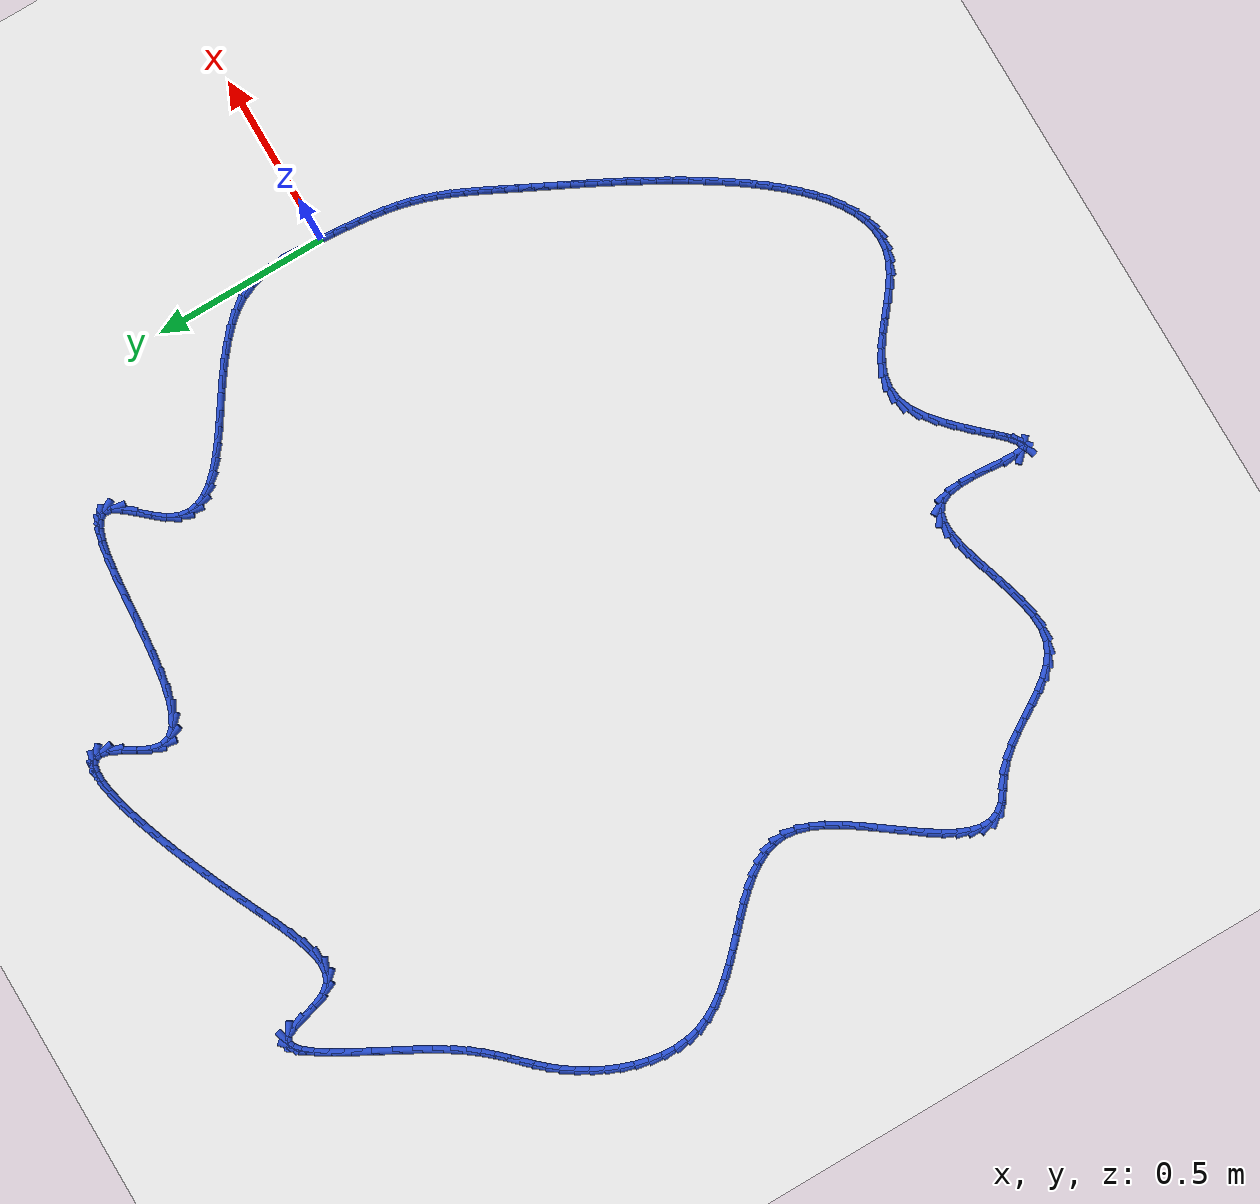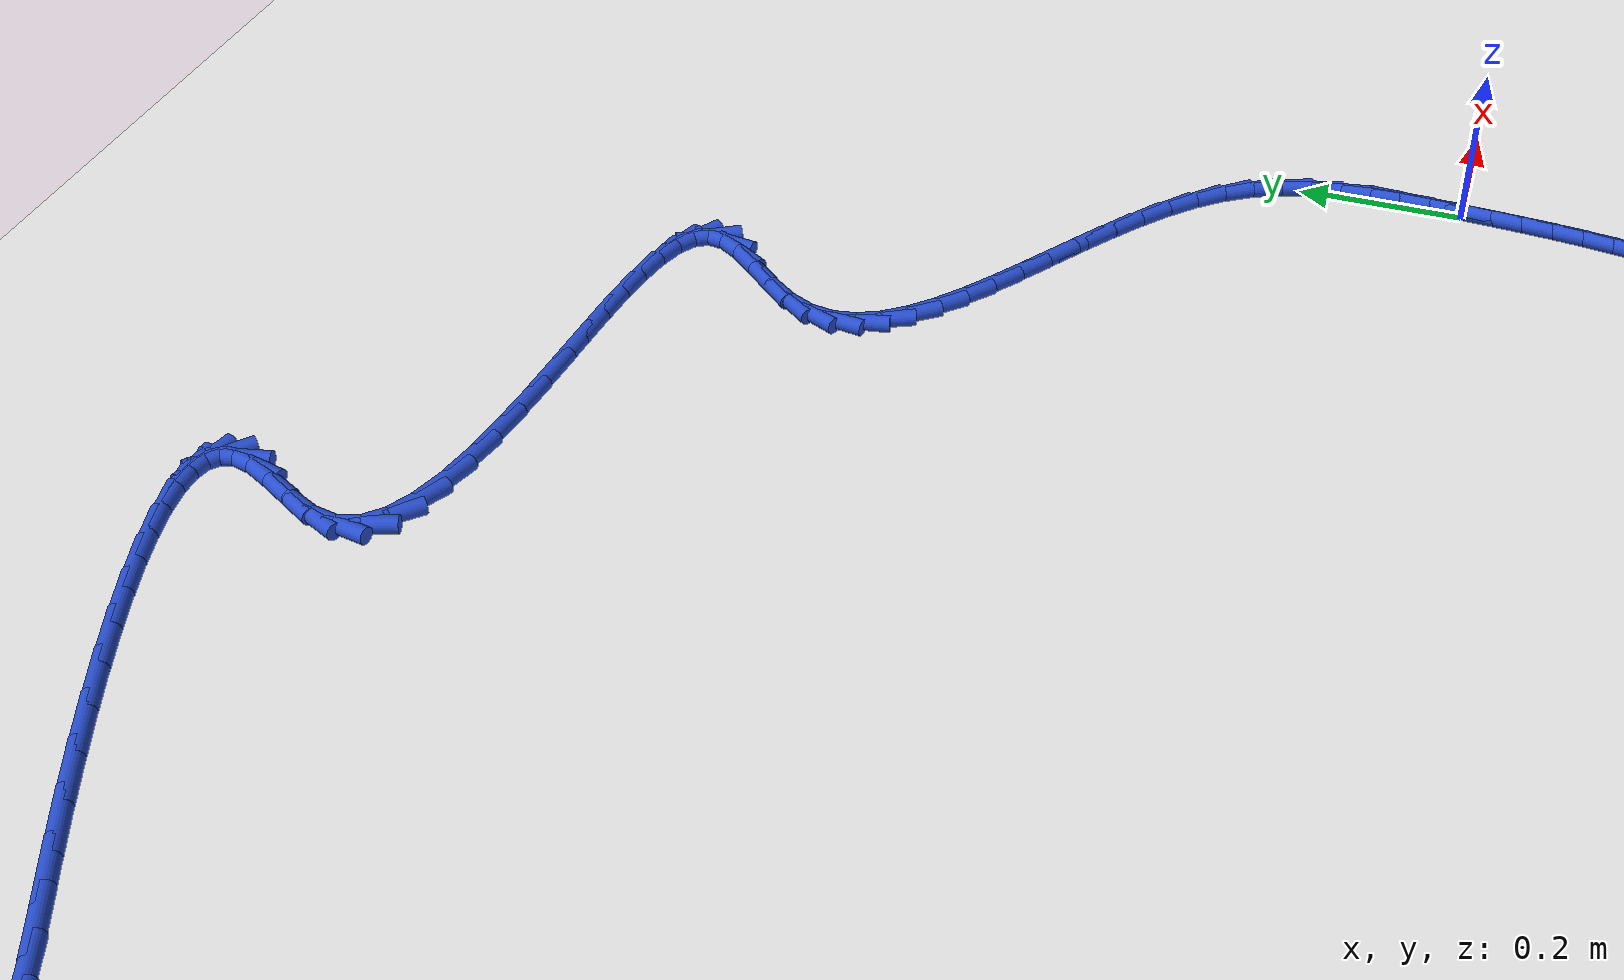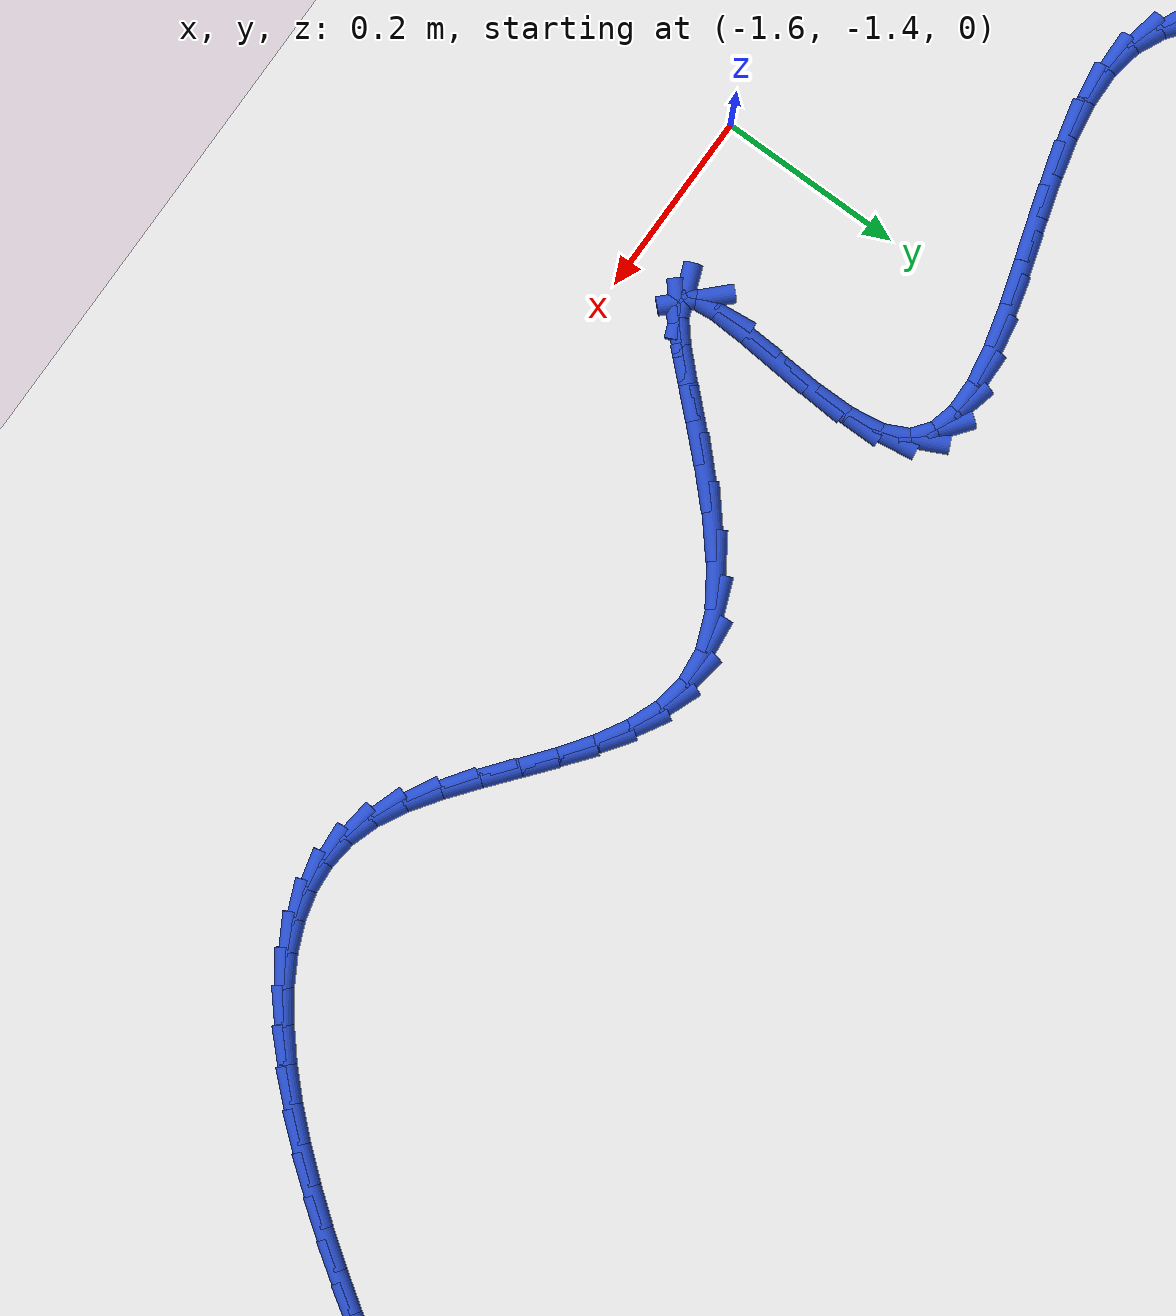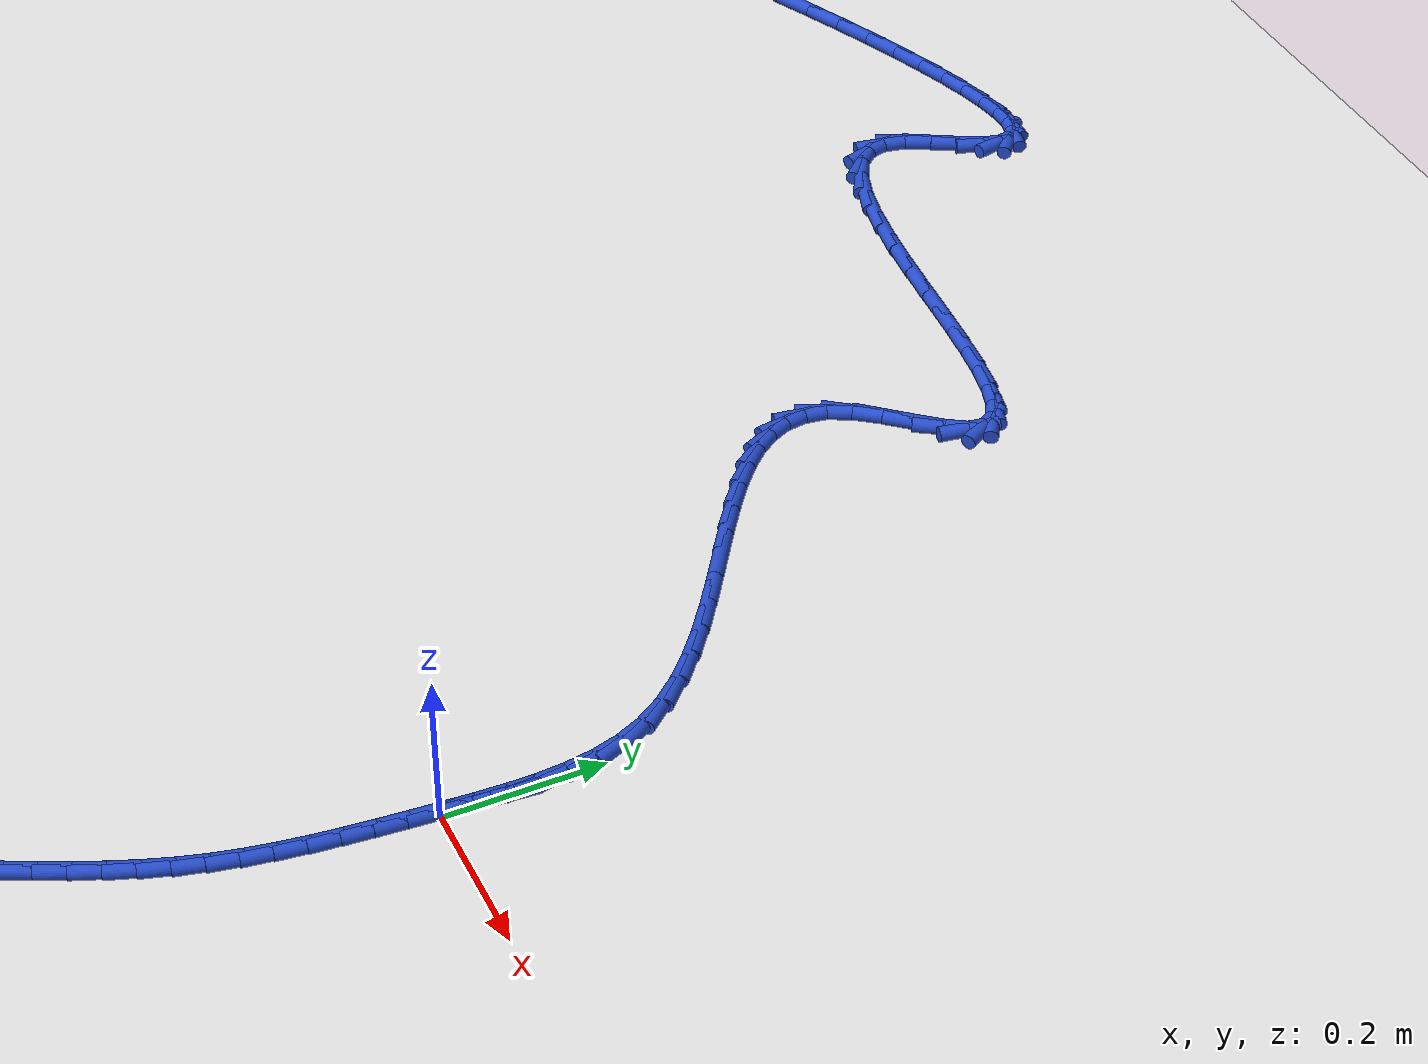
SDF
<sdf version="1.6">
 <world name="default">
  <light name="sun" type="directional">
   <pose>0 0 10 0 -0 0</pose>
   <diffuse>0.8 0.8 0.8 1</diffuse>
   <specular>0.2 0.2 0.2 1</specular>
   <attenuation>
    <range>1000</range>
    <constant>0.9</constant>
    <linear>0.01</linear>
    <quadratic>0.001</quadratic>
   </attenuation>
   <direction>-0.5 0.1 -0.9</direction>
  </light>
  <model name="ground_plane">
   <static>1</static>
   <link name="link">
    <collision name="collision">
     <geometry><plane><normal>0 0 1</normal><size>100 100</size></plane></geometry>
     <surface><friction><ode><mu>100</mu><mu2>50</mu2></ode></friction></surface>
    </collision>
    <visual name="visual">
     <cast_shadows>0</cast_shadows>
     <geometry><plane><normal>0 0 1</normal><size>100 100</size></plane></geometry>
     <material>
      <script><uri>file://media/materials/scripts/gazebo.material</uri><name>Gazebo/WhiteGlow</name></script>
     </material>
    </visual>
   </link>
  </model>
  <gravity>0 0 -9.8</gravity>
  <magnetic_field>6e-06 2.3e-05 -4.2e-05</magnetic_field>
  <atmosphere type="adiabatic"/>
  <physics name="default_physics" default="0" type="ode">
   <max_step_size>0.001</max_step_size>
   <real_time_factor>1</real_time_factor>
   <real_time_update_rate>1000</real_time_update_rate>
  </physics>
  <scene><ambient>0.4 0.4 0.4 1</ambient><background>0.7 0.7 0.7 1</background><shadows>1</shadows></scene>
  <spherical_coordinates>
   <surface_model>EARTH_WGS84</surface_model>
   <latitude_deg>0</latitude_deg>
   <longitude_deg>0</longitude_deg>
   <elevation>0</elevation>
   <heading_deg>0</heading_deg>
  </spherical_coordinates>
  <model name="line">
   <link name="link_0">
    <pose>8.673617379884035e-19 -5.551115123125783e-17 0.01 0 1.57 1.5075253190274285</pose>
    <collision name="collision">
     <geometry><cylinder><radius>0.01</radius><length>0.08</length></cylinder></geometry>
    </collision>
    <visual name="visual">
     <material>
      <script><name>Gazebo/Blue</name><uri>file://media/materials/scripts/gazebo.material</uri></script>
     </material>
     <geometry><cylinder><radius>0.01</radius><length>0.08</length></cylinder></geometry>
    </visual>
   </link>
   <link name="link_1">
    <pose>0.0024006974243786046 0.03789244310633456 0.01 0 1.57 1.5290202648854714</pose>
    <collision name="collision">
     <geometry><cylinder><radius>0.01</radius><length>0.08</length></cylinder></geometry>
    </collision>
    <visual name="visual">
     <material>
      <script><name>Gazebo/Blue</name><uri>file://media/materials/scripts/gazebo.material</uri></script>
     </material>
     <geometry><cylinder><radius>0.01</radius><length>0.08</length></cylinder></geometry>
    </visual>
   </link>
   <link name="link_2">
    <pose>0.003987087788672461 0.07584401890051412 0.01 0 1.57 -1.5689586023007087</pose>
    <collision name="collision">
     <geometry><cylinder><radius>0.01</radius><length>0.08</length></cylinder></geometry>
    </collision>
    <visual name="visual">
     <material>
      <script><name>Gazebo/Blue</name><uri>file://media/materials/scripts/gazebo.material</uri></script>
     </material>
     <geometry><cylinder><radius>0.01</radius><length>0.08</length></cylinder></geometry>
    </visual>
   </link>
   <link name="link_3">
    <pose>0.003917731223084836 0.11358443523018567 0.01 0 1.57 -1.5020210537201513</pose>
    <collision name="collision">
     <geometry><cylinder><radius>0.01</radius><length>0.08</length></cylinder></geometry>
    </collision>
    <visual name="visual">
     <material>
      <script><name>Gazebo/Blue</name><uri>file://media/materials/scripts/gazebo.material</uri></script>
     </material>
     <geometry><cylinder><radius>0.01</radius><length>0.08</length></cylinder></geometry>
    </visual>
   </link>
   <link name="link_4">
    <pose>0.0013511878578189931 0.150843399942996 0.01 0 1.57 -1.4104318224017498</pose>
    <collision name="collision">
     <geometry><cylinder><radius>0.01</radius><length>0.08</length></cylinder></geometry>
    </collision>
    <visual name="visual">
     <material>
      <script><name>Gazebo/Blue</name><uri>file://media/materials/scripts/gazebo.material</uri></script>
     </material>
     <geometry><cylinder><radius>0.01</radius><length>0.08</length></cylinder></geometry>
    </visual>
   </link>
   <link name="link_5">
    <pose>-0.004553982176921807 0.18735062088659205 0.01 0 1.57 -1.2938881794318415</pose>
    <collision name="collision">
     <geometry><cylinder><radius>0.01</radius><length>0.08</length></cylinder></geometry>
    </collision>
    <visual name="visual">
     <material>
      <script><name>Gazebo/Blue</name><uri>file://media/materials/scripts/gazebo.material</uri></script>
     </material>
     <geometry><cylinder><radius>0.01</radius><length>0.08</length></cylinder></geometry>
    </visual>
   </link>
   <link name="link_6">
    <pose>-0.014639218750934303 0.22283580590862082 0.01 0 1.57 -1.1547741205388387</pose>
    <collision name="collision">
     <geometry><cylinder><radius>0.01</radius><length>0.08</length></cylinder></geometry>
    </collision>
    <visual name="visual">
     <material>
      <script><name>Gazebo/Blue</name><uri>file://media/materials/scripts/gazebo.material</uri></script>
     </material>
     <geometry><cylinder><radius>0.01</radius><length>0.08</length></cylinder></geometry>
    </visual>
   </link>
   <link name="link_7">
    <pose>-0.02974596173401522 0.25702866285672893 0.01 0 1.57 -1.0014317657565566</pose>
    <collision name="collision">
     <geometry><cylinder><radius>0.01</radius><length>0.08</length></cylinder></geometry>
    </collision>
    <visual name="visual">
     <material>
      <script><name>Gazebo/Blue</name><uri>file://media/materials/scripts/gazebo.material</uri></script>
     </material>
     <geometry><cylinder><radius>0.01</radius><length>0.08</length></cylinder></geometry>
    </visual>
   </link>
   <link name="link_8">
    <pose>-0.05064300377911523 0.2896765970687816 0.01 0 1.57 -0.8663912121392355</pose>
    <collision name="collision">
     <geometry><cylinder><radius>0.01</radius><length>0.08</length></cylinder></geometry>
    </collision>
    <visual name="visual">
     <material>
      <script><name>Gazebo/Blue</name><uri>file://media/materials/scripts/gazebo.material</uri></script>
     </material>
     <geometry><cylinder><radius>0.01</radius><length>0.08</length></cylinder></geometry>
    </visual>
   </link>
   <link name="link_9">
    <pose>-0.07707347467329738 0.32077687422587503 0.01 0 1.57 -0.7654138585581325</pose>
    <collision name="collision">
     <geometry><cylinder><radius>0.01</radius><length>0.08</length></cylinder></geometry>
    </collision>
    <visual name="visual">
     <material>
      <script><name>Gazebo/Blue</name><uri>file://media/materials/scripts/gazebo.material</uri></script>
     </material>
     <geometry><cylinder><radius>0.01</radius><length>0.08</length></cylinder></geometry>
    </visual>
   </link>
   <link name="link_10">
    <pose>-0.10802119532142378 0.3505117342186976 0.01 0 1.57 -0.6923956295825017</pose>
    <collision name="collision">
     <geometry><cylinder><radius>0.01</radius><length>0.08</length></cylinder></geometry>
    </collision>
    <visual name="visual">
     <material>
      <script><name>Gazebo/Blue</name><uri>file://media/materials/scripts/gazebo.material</uri></script>
     </material>
     <geometry><cylinder><radius>0.01</radius><length>0.08</length></cylinder></geometry>
    </visual>
   </link>
   <link name="link_11">
    <pose>-0.14245212459521098 0.37906776828366845 0.01 0 1.57 -0.64182833404888</pose>
    <collision name="collision">
     <geometry><cylinder><radius>0.01</radius><length>0.08</length></cylinder></geometry>
    </collision>
    <visual name="visual">
     <material>
      <script><name>Gazebo/Blue</name><uri>file://media/materials/scripts/gazebo.material</uri></script>
     </material>
     <geometry><cylinder><radius>0.01</radius><length>0.08</length></cylinder></geometry>
    </visual>
   </link>
   <link name="link_12">
    <pose>-0.17933222136637558 0.40663156765720654 0.01 0 1.57 -0.6098754694298004</pose>
    <collision name="collision">
     <geometry><cylinder><radius>0.01</radius><length>0.08</length></cylinder></geometry>
    </collision>
    <visual name="visual">
     <material>
      <script><name>Gazebo/Blue</name><uri>file://media/materials/scripts/gazebo.material</uri></script>
     </material>
     <geometry><cylinder><radius>0.01</radius><length>0.08</length></cylinder></geometry>
    </visual>
   </link>
   <link name="link_13">
    <pose>-0.21762744450663402 0.4333897235757309 0.01 0 1.57 -0.5943284206412195</pose>
    <collision name="collision">
     <geometry><cylinder><radius>0.01</radius><length>0.08</length></cylinder></geometry>
    </collision>
    <visual name="visual">
     <material>
      <script><name>Gazebo/Blue</name><uri>file://media/materials/scripts/gazebo.material</uri></script>
     </material>
     <geometry><cylinder><radius>0.01</radius><length>0.08</length></cylinder></geometry>
    </visual>
   </link>
   <link name="link_14">
    <pose>-0.2563037528877031 0.45952882727566086 0.01 0 1.57 -0.594487897480302</pose>
    <collision name="collision">
     <geometry><cylinder><radius>0.01</radius><length>0.08</length></cylinder></geometry>
    </collision>
    <visual name="visual">
     <material>
      <script><name>Gazebo/Blue</name><uri>file://media/materials/scripts/gazebo.material</uri></script>
     </material>
     <geometry><cylinder><radius>0.01</radius><length>0.08</length></cylinder></geometry>
    </visual>
   </link>
   <link name="link_15">
    <pose>-0.29432710538129914 0.485235469993415 0.01 0 1.57 -0.6111935539686418</pose>
    <collision name="collision">
     <geometry><cylinder><radius>0.01</radius><length>0.08</length></cylinder></geometry>
    </collision>
    <visual name="visual">
     <material>
      <script><name>Gazebo/Blue</name><uri>file://media/materials/scripts/gazebo.material</uri></script>
     </material>
     <geometry><cylinder><radius>0.01</radius><length>0.08</length></cylinder></geometry>
    </visual>
   </link>
   <link name="link_16">
    <pose>-0.33066346085913895 0.5106962429654127 0.01 0 1.57 -0.6471088264313417</pose>
    <collision name="collision">
     <geometry><cylinder><radius>0.01</radius><length>0.08</length></cylinder></geometry>
    </collision>
    <visual name="visual">
     <material>
      <script><name>Gazebo/Blue</name><uri>file://media/materials/scripts/gazebo.material</uri></script>
     </material>
     <geometry><cylinder><radius>0.01</radius><length>0.08</length></cylinder></geometry>
    </visual>
   </link>
   <link name="link_17">
    <pose>-0.3642787781929391 0.5360977374280731 0.01 0 1.57 -0.7073568498102262</pose>
    <collision name="collision">
     <geometry><cylinder><radius>0.01</radius><length>0.08</length></cylinder></geometry>
    </collision>
    <visual name="visual">
     <material>
      <script><name>Gazebo/Blue</name><uri>file://media/materials/scripts/gazebo.material</uri></script>
     </material>
     <geometry><cylinder><radius>0.01</radius><length>0.08</length></cylinder></geometry>
    </visual>
   </link>
   <link name="link_18">
    <pose>-0.394139016254416 0.5616265446178148 0.01 0 1.57 -0.8005518936840011</pose>
    <collision name="collision">
     <geometry><cylinder><radius>0.01</radius><length>0.08</length></cylinder></geometry>
    </collision>
    <visual name="visual">
     <material>
      <script><name>Gazebo/Blue</name><uri>file://media/materials/scripts/gazebo.material</uri></script>
     </material>
     <geometry><cylinder><radius>0.01</radius><length>0.08</length></cylinder></geometry>
    </visual>
   </link>
   <link name="link_19">
    <pose>-0.4192101339152863 0.5874692557710572 0.01 0 1.57 -0.9397874312750841</pose>
    <collision name="collision">
     <geometry><cylinder><radius>0.01</radius><length>0.08</length></cylinder></geometry>
    </collision>
    <visual name="visual">
     <material>
      <script><name>Gazebo/Blue</name><uri>file://media/materials/scripts/gazebo.material</uri></script>
     </material>
     <geometry><cylinder><radius>0.01</radius><length>0.08</length></cylinder></geometry>
    </visual>
   </link>
   <link name="link_20">
    <pose>-0.43845809004726666 0.6138124621242195 0.01 0 1.57 -1.1409768995910816</pose>
    <collision name="collision">
     <geometry><cylinder><radius>0.01</radius><length>0.08</length></cylinder></geometry>
    </collision>
    <visual name="visual">
     <material>
      <script><name>Gazebo/Blue</name><uri>file://media/materials/scripts/gazebo.material</uri></script>
     </material>
     <geometry><cylinder><radius>0.01</radius><length>0.08</length></cylinder></geometry>
    </visual>
   </link>
   <link name="link_21">
    <pose>-0.4508488435220736 0.6408427549137203 0.01 0 1.57 -1.4109226978637774</pose>
    <collision name="collision">
     <geometry><cylinder><radius>0.01</radius><length>0.08</length></cylinder></geometry>
    </collision>
    <visual name="visual">
     <material>
      <script><name>Gazebo/Blue</name><uri>file://media/materials/scripts/gazebo.material</uri></script>
     </material>
     <geometry><cylinder><radius>0.01</radius><length>0.08</length></cylinder></geometry>
    </visual>
   </link>
   <link name="link_22">
    <pose>-0.45534835321142353 0.6687467253759789 0.01 0 1.57 1.4191677931692994</pose>
    <collision name="collision">
     <geometry><cylinder><radius>0.01</radius><length>0.08</length></cylinder></geometry>
    </collision>
    <visual name="visual">
     <material>
      <script><name>Gazebo/Blue</name><uri>file://media/materials/scripts/gazebo.material</uri></script>
     </material>
     <geometry><cylinder><radius>0.01</radius><length>0.08</length></cylinder></geometry>
    </visual>
   </link>
   <link name="link_23">
    <pose>-0.4509225779870332 0.6977109647474142 0.01 0 1.57 1.1265887744590974</pose>
    <collision name="collision">
     <geometry><cylinder><radius>0.01</radius><length>0.08</length></cylinder></geometry>
    </collision>
    <visual name="visual">
     <material>
      <script><name>Gazebo/Blue</name><uri>file://media/materials/scripts/gazebo.material</uri></script>
     </material>
     <geometry><cylinder><radius>0.01</radius><length>0.08</length></cylinder></geometry>
    </visual>
   </link>
   <link name="link_24">
    <pose>-0.4365450232952983 0.7279203001907419 0.01 0 1.57 0.9265132472743725</pose>
    <collision name="collision">
     <geometry><cylinder><radius>0.01</radius><length>0.08</length></cylinder></geometry>
    </collision>
    <visual name="visual">
     <material>
      <script><name>Gazebo/Blue</name><uri>file://media/materials/scripts/gazebo.material</uri></script>
     </material>
     <geometry><cylinder><radius>0.01</radius><length>0.08</length></cylinder></geometry>
    </visual>
   </link>
   <link name="link_25">
    <pose>-0.4131150955645314 0.7591093637241842 0.01 0 1.57 0.8499098955715528</pose>
    <collision name="collision">
     <geometry><cylinder><radius>0.01</radius><length>0.08</length></cylinder></geometry>
    </collision>
    <visual name="visual">
     <material>
      <script><name>Gazebo/Blue</name><uri>file://media/materials/scripts/gazebo.material</uri></script>
     </material>
     <geometry><cylinder><radius>0.01</radius><length>0.08</length></cylinder></geometry>
    </visual>
   </link>
   <link name="link_26">
    <pose>-0.38600149579867293 0.789968053116307 0.01 0 1.57 0.8645799931508453</pose>
    <collision name="collision">
     <geometry><cylinder><radius>0.01</radius><length>0.08</length></cylinder></geometry>
    </collision>
    <visual name="visual">
     <material>
      <script><name>Gazebo/Blue</name><uri>file://media/materials/scripts/gazebo.material</uri></script>
     </material>
     <geometry><cylinder><radius>0.01</radius><length>0.08</length></cylinder></geometry>
    </visual>
   </link>
   <link name="link_27">
    <pose>-0.36120529643232446 0.8190384441291078 0.01 0 1.57 1.0028507828849151</pose>
    <collision name="collision">
     <geometry><cylinder><radius>0.01</radius><length>0.08</length></cylinder></geometry>
    </collision>
    <visual name="visual">
     <material>
      <script><name>Gazebo/Blue</name><uri>file://media/materials/scripts/gazebo.material</uri></script>
     </material>
     <geometry><cylinder><radius>0.01</radius><length>0.08</length></cylinder></geometry>
    </visual>
   </link>
   <link name="link_28">
    <pose>-0.34472756990008724 0.8448626125245833 0.01 0 1.57 1.4241262407742952</pose>
    <collision name="collision">
     <geometry><cylinder><radius>0.01</radius><length>0.08</length></cylinder></geometry>
    </collision>
    <visual name="visual">
     <material>
      <script><name>Gazebo/Blue</name><uri>file://media/materials/scripts/gazebo.material</uri></script>
     </material>
     <geometry><cylinder><radius>0.01</radius><length>0.08</length></cylinder></geometry>
    </visual>
   </link>
   <link name="link_29">
    <pose>-0.34156777465274174 0.8662514642827709 0.01 0 1.57 -1.0385326744617382</pose>
    <collision name="collision">
     <geometry><cylinder><radius>0.01</radius><length>0.08</length></cylinder></geometry>
    </collision>
    <visual name="visual">
     <material>
      <script><name>Gazebo/Blue</name><uri>file://media/materials/scripts/gazebo.material</uri></script>
     </material>
     <geometry><cylinder><radius>0.01</radius><length>0.08</length></cylinder></geometry>
    </visual>
   </link>
   <link name="link_30">
    <pose>-0.3516540762188279 0.8833770253401521 0.01 0 1.57 -0.5561707207859877</pose>
    <collision name="collision">
     <geometry><cylinder><radius>0.01</radius><length>0.08</length></cylinder></geometry>
    </collision>
    <visual name="visual">
     <material>
      <script><name>Gazebo/Blue</name><uri>file://media/materials/scripts/gazebo.material</uri></script>
     </material>
     <geometry><cylinder><radius>0.01</radius><length>0.08</length></cylinder></geometry>
    </visual>
   </link>
   <link name="link_31">
    <pose>-0.3733134287240263 0.8968410820174597 0.01 0 1.57 -0.31846515100283507</pose>
    <collision name="collision">
     <geometry><cylinder><radius>0.01</radius><length>0.08</length></cylinder></geometry>
    </collision>
    <visual name="visual">
     <material>
      <script><name>Gazebo/Blue</name><uri>file://media/materials/scripts/gazebo.material</uri></script>
     </material>
     <geometry><cylinder><radius>0.01</radius><length>0.08</length></cylinder></geometry>
    </visual>
   </link>
   <link name="link_32">
    <pose>-0.4048721725801135 0.9072455853544157 0.01 0 1.57 -0.197154004233897</pose>
    <collision name="collision">
     <geometry><cylinder><radius>0.01</radius><length>0.08</length></cylinder></geometry>
    </collision>
    <visual name="visual">
     <material>
      <script><name>Gazebo/Blue</name><uri>file://media/materials/scripts/gazebo.material</uri></script>
     </material>
     <geometry><cylinder><radius>0.01</radius><length>0.08</length></cylinder></geometry>
    </visual>
   </link>
   <link name="link_33">
    <pose>-0.444656648198866 0.9151924863907421 0.01 0 1.57 -0.13070722965840106</pose>
    <collision name="collision">
     <geometry><cylinder><radius>0.01</radius><length>0.08</length></cylinder></geometry>
    </collision>
    <visual name="visual">
     <material>
      <script><name>Gazebo/Blue</name><uri>file://media/materials/scripts/gazebo.material</uri></script>
     </material>
     <geometry><cylinder><radius>0.01</radius><length>0.08</length></cylinder></geometry>
    </visual>
   </link>
   <link name="link_34">
    <pose>-0.49099319599206065 0.9212837361661609 0.01 0 1.57 -0.09417637619817003</pose>
    <collision name="collision">
     <geometry><cylinder><radius>0.01</radius><length>0.08</length></cylinder></geometry>
    </collision>
    <visual name="visual">
     <material>
      <script><name>Gazebo/Blue</name><uri>file://media/materials/scripts/gazebo.material</uri></script>
     </material>
     <geometry><cylinder><radius>0.01</radius><length>0.08</length></cylinder></geometry>
    </visual>
   </link>
   <link name="link_35">
    <pose>-0.5422081563714738 0.9261212857203935 0.01 0 1.57 -0.07676583691806407</pose>
    <collision name="collision">
     <geometry><cylinder><radius>0.01</radius><length>0.08</length></cylinder></geometry>
    </collision>
    <visual name="visual">
     <material>
      <script><name>Gazebo/Blue</name><uri>file://media/materials/scripts/gazebo.material</uri></script>
     </material>
     <geometry><cylinder><radius>0.01</radius><length>0.08</length></cylinder></geometry>
    </visual>
   </link>
   <link name="link_36">
    <pose>-0.5966278697488823 0.9303070860931625 0.01 0 1.57 -0.07378791071253317</pose>
    <collision name="collision">
     <geometry><cylinder><radius>0.01</radius><length>0.08</length></cylinder></geometry>
    </collision>
    <visual name="visual">
     <material>
      <script><name>Gazebo/Blue</name><uri>file://media/materials/scripts/gazebo.material</uri></script>
     </material>
     <geometry><cylinder><radius>0.01</radius><length>0.08</length></cylinder></geometry>
    </visual>
   </link>
   <link name="link_37">
    <pose>-0.6525786765360627 0.9344430883241895 0.01 0 1.57 -0.08380794231501582</pose>
    <collision name="collision">
     <geometry><cylinder><radius>0.01</radius><length>0.08</length></cylinder></geometry>
    </collision>
    <visual name="visual">
     <material>
      <script><name>Gazebo/Blue</name><uri>file://media/materials/scripts/gazebo.material</uri></script>
     </material>
     <geometry><cylinder><radius>0.01</radius><length>0.08</length></cylinder></geometry>
    </visual>
   </link>
   <link name="link_38">
    <pose>-0.7083869171447914 0.9391312434531967 0.01 0 1.57 -0.10778661451439918</pose>
    <collision name="collision">
     <geometry><cylinder><radius>0.01</radius><length>0.08</length></cylinder></geometry>
    </collision>
    <visual name="visual">
     <material>
      <script><name>Gazebo/Blue</name><uri>file://media/materials/scripts/gazebo.material</uri></script>
     </material>
     <geometry><cylinder><radius>0.01</radius><length>0.08</length></cylinder></geometry>
    </visual>
   </link>
   <link name="link_39">
    <pose>-0.7623789319868453 0.9449735025199053 0.01 0 1.57 -0.14933521840631078</pose>
    <collision name="collision">
     <geometry><cylinder><radius>0.01</radius><length>0.08</length></cylinder></geometry>
    </collision>
    <visual name="visual">
     <material>
      <script><name>Gazebo/Blue</name><uri>file://media/materials/scripts/gazebo.material</uri></script>
     </material>
     <geometry><cylinder><radius>0.01</radius><length>0.08</length></cylinder></geometry>
    </visual>
   </link>
   <link name="link_40">
    <pose>-0.8128810614740011 0.9525718165640382 0.01 0 1.57 -0.21616804262895564</pose>
    <collision name="collision">
     <geometry><cylinder><radius>0.01</radius><length>0.08</length></cylinder></geometry>
    </collision>
    <visual name="visual">
     <material>
      <script><name>Gazebo/Blue</name><uri>file://media/materials/scripts/gazebo.material</uri></script>
     </material>
     <geometry><cylinder><radius>0.01</radius><length>0.08</length></cylinder></geometry>
    </visual>
   </link>
   <link name="link_41">
    <pose>-0.8582196460180352 0.9625281366253167 0.01 0 1.57 -0.32367743674897254</pose>
    <collision name="collision">
     <geometry><cylinder><radius>0.01</radius><length>0.08</length></cylinder></geometry>
    </collision>
    <visual name="visual">
     <material>
      <script><name>Gazebo/Blue</name><uri>file://media/materials/scripts/gazebo.material</uri></script>
     </material>
     <geometry><cylinder><radius>0.01</radius><length>0.08</length></cylinder></geometry>
    </visual>
   </link>
   <link name="link_42">
    <pose>-0.8967210260307243 0.9754444137434628 0.01 0 1.57 -0.502418190944188</pose>
    <collision name="collision">
     <geometry><cylinder><radius>0.01</radius><length>0.08</length></cylinder></geometry>
    </collision>
    <visual name="visual">
     <material>
      <script><name>Gazebo/Blue</name><uri>file://media/materials/scripts/gazebo.material</uri></script>
     </material>
     <geometry><cylinder><radius>0.01</radius><length>0.08</length></cylinder></geometry>
    </visual>
   </link>
   <link name="link_43">
    <pose>-0.9267115419238452 0.9919225989581986 0.01 0 1.57 -0.806065004185008</pose>
    <collision name="collision">
     <geometry><cylinder><radius>0.01</radius><length>0.08</length></cylinder></geometry>
    </collision>
    <visual name="visual">
     <material>
      <script><name>Gazebo/Blue</name><uri>file://media/materials/scripts/gazebo.material</uri></script>
     </material>
     <geometry><cylinder><radius>0.01</radius><length>0.08</length></cylinder></geometry>
    </visual>
   </link>
   <link name="link_44">
    <pose>-0.9465175341091742 1.012564643309246 0.01 0 1.57 -1.2676298551796483</pose>
    <collision name="collision">
     <geometry><cylinder><radius>0.01</radius><length>0.08</length></cylinder></geometry>
    </collision>
    <visual name="visual">
     <material>
      <script><name>Gazebo/Blue</name><uri>file://media/materials/scripts/gazebo.material</uri></script>
     </material>
     <geometry><cylinder><radius>0.01</radius><length>0.08</length></cylinder></geometry>
    </visual>
   </link>
   <link name="link_45">
    <pose>-0.954465342998488 1.0379724978363267 0.01 0 1.57 1.39590290702077</pose>
    <collision name="collision">
     <geometry><cylinder><radius>0.01</radius><length>0.08</length></cylinder></geometry>
    </collision>
    <visual name="visual">
     <material>
      <script><name>Gazebo/Blue</name><uri>file://media/materials/scripts/gazebo.material</uri></script>
     </material>
     <geometry><cylinder><radius>0.01</radius><length>0.08</length></cylinder></geometry>
    </visual>
   </link>
   <link name="link_46">
    <pose>-0.9490411559229682 1.068669876234632 0.01 0 1.57 1.1337649181963538</pose>
    <collision name="collision">
     <geometry><cylinder><radius>0.01</radius><length>0.08</length></cylinder></geometry>
    </collision>
    <visual name="visual">
     <material>
      <script><name>Gazebo/Blue</name><uri>file://media/materials/scripts/gazebo.material</uri></script>
     </material>
     <geometry><cylinder><radius>0.01</radius><length>0.08</length></cylinder></geometry>
    </visual>
   </link>
   <link name="link_47">
    <pose>-0.9329493993433 1.1031158679368374 0.01 0 1.57 1.0552168070613144</pose>
    <collision name="collision">
     <geometry><cylinder><radius>0.01</radius><length>0.08</length></cylinder></geometry>
    </collision>
    <visual name="visual">
     <material>
      <script><name>Gazebo/Blue</name><uri>file://media/materials/scripts/gazebo.material</uri></script>
     </material>
     <geometry><cylinder><radius>0.01</radius><length>0.08</length></cylinder></geometry>
    </visual>
   </link>
   <link name="link_48">
    <pose>-0.9134376560663752 1.137545906832915 0.01 0 1.57 1.102155173140251</pose>
    <collision name="collision">
     <geometry><cylinder><radius>0.01</radius><length>0.08</length></cylinder></geometry>
    </collision>
    <visual name="visual">
     <material>
      <script><name>Gazebo/Blue</name><uri>file://media/materials/scripts/gazebo.material</uri></script>
     </material>
     <geometry><cylinder><radius>0.01</radius><length>0.08</length></cylinder></geometry>
    </visual>
   </link>
   <link name="link_49">
    <pose>-0.8979762566902787 1.168086483750758 0.01 0 1.57 1.3291386056906196</pose>
    <collision name="collision">
     <geometry><cylinder><radius>0.01</radius><length>0.08</length></cylinder></geometry>
    </collision>
    <visual name="visual">
     <material>
      <script><name>Gazebo/Blue</name><uri>file://media/materials/scripts/gazebo.material</uri></script>
     </material>
     <geometry><cylinder><radius>0.01</radius><length>0.08</length></cylinder></geometry>
    </visual>
   </link>
   <link name="link_50">
    <pose>-0.8921126494063587 1.1918764066381438 0.01 0 1.57 -1.3493950889043413</pose>
    <collision name="collision">
     <geometry><cylinder><radius>0.01</radius><length>0.08</length></cylinder></geometry>
    </collision>
    <visual name="visual">
     <material>
      <script><name>Gazebo/Blue</name><uri>file://media/materials/scripts/gazebo.material</uri></script>
     </material>
     <geometry><cylinder><radius>0.01</radius><length>0.08</length></cylinder></geometry>
    </visual>
   </link>
   <link name="link_51">
    <pose>-0.8959492516949755 1.2089210642528503 0.01 0 1.57 -0.7058133783352732</pose>
    <collision name="collision">
     <geometry><cylinder><radius>0.01</radius><length>0.08</length></cylinder></geometry>
    </collision>
    <visual name="visual">
     <material>
      <script><name>Gazebo/Blue</name><uri>file://media/materials/scripts/gazebo.material</uri></script>
     </material>
     <geometry><cylinder><radius>0.01</radius><length>0.08</length></cylinder></geometry>
    </visual>
   </link>
   <link name="link_52">
    <pose>-0.9086313748793773 1.2197297216921528 0.01 0 1.57 -0.2410450929915201</pose>
    <collision name="collision">
     <geometry><cylinder><radius>0.01</radius><length>0.08</length></cylinder></geometry>
    </collision>
    <visual name="visual">
     <material>
      <script><name>Gazebo/Blue</name><uri>file://media/materials/scripts/gazebo.material</uri></script>
     </material>
     <geometry><cylinder><radius>0.01</radius><length>0.08</length></cylinder></geometry>
    </visual>
   </link>
   <link name="link_53">
    <pose>-0.9293043302828121 1.2248116440533283 0.01 0 1.57 0.004874179724751504</pose>
    <collision name="collision">
     <geometry><cylinder><radius>0.01</radius><length>0.08</length></cylinder></geometry>
    </collision>
    <visual name="visual">
     <material>
      <script><name>Gazebo/Blue</name><uri>file://media/materials/scripts/gazebo.material</uri></script>
     </material>
     <geometry><cylinder><radius>0.01</radius><length>0.08</length></cylinder></geometry>
    </visual>
   </link>
   <link name="link_54">
    <pose>-0.9571134292285278 1.2246760964336518 0.01 0 1.57 0.14114016267156324</pose>
    <collision name="collision">
     <geometry><cylinder><radius>0.01</radius><length>0.08</length></cylinder></geometry>
    </collision>
    <visual name="visual">
     <material>
      <script><name>Gazebo/Blue</name><uri>file://media/materials/scripts/gazebo.material</uri></script>
     </material>
     <geometry><cylinder><radius>0.01</radius><length>0.08</length></cylinder></geometry>
    </visual>
   </link>
   <link name="link_55">
    <pose>-0.9912039830397729 1.2198323439304009 0.01 0 1.57 0.22495554003833673</pose>
    <collision name="collision">
     <geometry><cylinder><radius>0.01</radius><length>0.08</length></cylinder></geometry>
    </collision>
    <visual name="visual">
     <material>
      <script><name>Gazebo/Blue</name><uri>file://media/materials/scripts/gazebo.material</uri></script>
     </material>
     <geometry><cylinder><radius>0.01</radius><length>0.08</length></cylinder></geometry>
    </visual>
   </link>
   <link name="link_56">
    <pose>-1.0307213030397948 1.2107896516408503 0.01 0 1.57 0.28113652876491724</pose>
    <collision name="collision">
     <geometry><cylinder><radius>0.01</radius><length>0.08</length></cylinder></geometry>
    </collision>
    <visual name="visual">
     <material>
      <script><name>Gazebo/Blue</name><uri>file://media/materials/scripts/gazebo.material</uri></script>
     </material>
     <geometry><cylinder><radius>0.01</radius><length>0.08</length></cylinder></geometry>
    </visual>
   </link>
   <link name="link_57">
    <pose>-1.074810700551842 1.1980572846622763 0.01 0 1.57 0.3213209097286658</pose>
    <collision name="collision">
     <geometry><cylinder><radius>0.01</radius><length>0.08</length></cylinder></geometry>
    </collision>
    <visual name="visual">
     <material>
      <script><name>Gazebo/Blue</name><uri>file://media/materials/scripts/gazebo.material</uri></script>
     </material>
     <geometry><cylinder><radius>0.01</radius><length>0.08</length></cylinder></geometry>
    </visual>
   </link>
   <link name="link_58">
    <pose>-1.1226174868991625 1.1821445080919561 0.01 0 1.57 0.3515336775595312</pose>
    <collision name="collision">
     <geometry><cylinder><radius>0.01</radius><length>0.08</length></cylinder></geometry>
    </collision>
    <visual name="visual">
     <material>
      <script><name>Gazebo/Blue</name><uri>file://media/materials/scripts/gazebo.material</uri></script>
     </material>
     <geometry><cylinder><radius>0.01</radius><length>0.08</length></cylinder></geometry>
    </visual>
   </link>
   <link name="link_59">
    <pose>-1.1732869734050047 1.1635605870271646 0.01 0 1.57 0.3751731866837851</pose>
    <collision name="collision">
     <geometry><cylinder><radius>0.01</radius><length>0.08</length></cylinder></geometry>
    </collision>
    <visual name="visual">
     <material>
      <script><name>Gazebo/Blue</name><uri>file://media/materials/scripts/gazebo.material</uri></script>
     </material>
     <geometry><cylinder><radius>0.01</radius><length>0.08</length></cylinder></geometry>
    </visual>
   </link>
   <link name="link_60">
    <pose>-1.2259644713926154 1.1428147865651785 0.01 0 1.57 0.3942988432691593</pose>
    <collision name="collision">
     <geometry><cylinder><radius>0.01</radius><length>0.08</length></cylinder></geometry>
    </collision>
    <visual name="visual">
     <material>
      <script><name>Gazebo/Blue</name><uri>file://media/materials/scripts/gazebo.material</uri></script>
     </material>
     <geometry><cylinder><radius>0.01</radius><length>0.08</length></cylinder></geometry>
    </visual>
   </link>
   <link name="link_61">
    <pose>-1.2797952921852445 1.1204163718032736 0.01 0 1.57 0.41023948761265855</pose>
    <collision name="collision">
     <geometry><cylinder><radius>0.01</radius><length>0.08</length></cylinder></geometry>
    </collision>
    <visual name="visual">
     <material>
      <script><name>Gazebo/Blue</name><uri>file://media/materials/scripts/gazebo.material</uri></script>
     </material>
     <geometry><cylinder><radius>0.01</radius><length>0.08</length></cylinder></geometry>
    </visual>
   </link>
   <link name="link_62">
    <pose>-1.3339247471061382 1.0968746078387264 0.01 0 1.57 0.4239061404555395</pose>
    <collision name="collision">
     <geometry><cylinder><radius>0.01</radius><length>0.08</length></cylinder></geometry>
    </collision>
    <visual name="visual">
     <material>
      <script><name>Gazebo/Blue</name><uri>file://media/materials/scripts/gazebo.material</uri></script>
     </material>
     <geometry><cylinder><radius>0.01</radius><length>0.08</length></cylinder></geometry>
    </visual>
   </link>
   <link name="link_63">
    <pose>-1.3874981474785462 1.0726987597688122 0.01 0 1.57 0.43596724969782996</pose>
    <collision name="collision">
     <geometry><cylinder><radius>0.01</radius><length>0.08</length></cylinder></geometry>
    </collision>
    <visual name="visual">
     <material>
      <script><name>Gazebo/Blue</name><uri>file://media/materials/scripts/gazebo.material</uri></script>
     </material>
     <geometry><cylinder><radius>0.01</radius><length>0.08</length></cylinder></geometry>
    </visual>
   </link>
   <link name="link_64">
    <pose>-1.4396608046257147 1.048398092690808 0.01 0 1.57 0.44550470599834224</pose>
    <collision name="collision">
     <geometry><cylinder><radius>0.01</radius><length>0.08</length></cylinder></geometry>
    </collision>
    <visual name="visual">
     <material>
      <script><name>Gazebo/Blue</name><uri>file://media/materials/scripts/gazebo.material</uri></script>
     </material>
     <geometry><cylinder><radius>0.01</radius><length>0.08</length></cylinder></geometry>
    </visual>
   </link>
   <link name="link_65">
    <pose>-1.4895843338457193 1.0245584689454401 0.01 0 1.57 0.4387814823470439</pose>
    <collision name="collision">
     <geometry><cylinder><radius>0.01</radius><length>0.08</length></cylinder></geometry>
    </collision>
    <visual name="visual">
     <material>
      <script><name>Gazebo/Blue</name><uri>file://media/materials/scripts/gazebo.material</uri></script>
     </material>
     <geometry><cylinder><radius>0.01</radius><length>0.08</length></cylinder></geometry>
    </visual>
   </link>
   <link name="link_66">
    <pose>-1.5366779892381162 1.0024577556845238 0.01 0 1.57 0.4038404943172151</pose>
    <collision name="collision">
     <geometry><cylinder><radius>0.01</radius><length>0.08</length></cylinder></geometry>
    </collision>
    <visual name="visual">
     <material>
      <script><name>Gazebo/Blue</name><uri>file://media/materials/scripts/gazebo.material</uri></script>
     </material>
     <geometry><cylinder><radius>0.01</radius><length>0.08</length></cylinder></geometry>
    </visual>
   </link>
   <link name="link_67">
    <pose>-1.5804771705634035 0.9837411565542822 0.01 0 1.57 0.3293017964491968</pose>
    <collision name="collision">
     <geometry><cylinder><radius>0.01</radius><length>0.08</length></cylinder></geometry>
    </collision>
    <visual name="visual">
     <material>
      <script><name>Gazebo/Blue</name><uri>file://media/materials/scripts/gazebo.material</uri></script>
     </material>
     <geometry><cylinder><radius>0.01</radius><length>0.08</length></cylinder></geometry>
    </visual>
   </link>
   <link name="link_68">
    <pose>-1.6205184385784936 0.970057256025517 0.01 0 1.57 0.19306018312066153</pose>
    <collision name="collision">
     <geometry><cylinder><radius>0.01</radius><length>0.08</length></cylinder></geometry>
    </collision>
    <visual name="visual">
     <material>
      <script><name>Gazebo/Blue</name><uri>file://media/materials/scripts/gazebo.material</uri></script>
     </material>
     <geometry><cylinder><radius>0.01</radius><length>0.08</length></cylinder></geometry>
    </visual>
   </link>
   <link name="link_69">
    <pose>-1.6563383540402936 0.963054638569029 0.01 0 1.57 -0.0426029141138185</pose>
    <collision name="collision">
     <geometry><cylinder><radius>0.01</radius><length>0.08</length></cylinder></geometry>
    </collision>
    <visual name="visual">
     <material>
      <script><name>Gazebo/Blue</name><uri>file://media/materials/scripts/gazebo.material</uri></script>
     </material>
     <geometry><cylinder><radius>0.01</radius><length>0.08</length></cylinder></geometry>
    </visual>
   </link>
   <link name="link_70">
    <pose>-1.687473477705714 0.9643818886556195 0.01 0 1.57 -0.4103555794179641</pose>
    <collision name="collision">
     <geometry><cylinder><radius>0.01</radius><length>0.08</length></cylinder></geometry>
    </collision>
    <visual name="visual">
     <material>
      <script><name>Gazebo/Blue</name><uri>file://media/materials/scripts/gazebo.material</uri></script>
     </material>
     <geometry><cylinder><radius>0.01</radius><length>0.08</length></cylinder></geometry>
    </visual>
   </link>
   <link name="link_71">
    <pose>-1.7134603703316638 0.9756875907560896 0.01 0 1.57 -0.8443788427989958</pose>
    <collision name="collision">
     <geometry><cylinder><radius>0.01</radius><length>0.08</length></cylinder></geometry>
    </collision>
    <visual name="visual">
     <material>
      <script><name>Gazebo/Blue</name><uri>file://media/materials/scripts/gazebo.material</uri></script>
     </material>
     <geometry><cylinder><radius>0.01</radius><length>0.08</length></cylinder></geometry>
    </visual>
   </link>
   <link name="link_72">
    <pose>-1.733835643924174 0.9986201561725705 0.01 0 1.57 -1.1625798326579104</pose>
    <collision name="collision">
     <geometry><cylinder><radius>0.01</radius><length>0.08</length></cylinder></geometry>
    </collision>
    <visual name="visual">
     <material>
      <script><name>Gazebo/Blue</name><uri>file://media/materials/scripts/gazebo.material</uri></script>
     </material>
     <geometry><cylinder><radius>0.01</radius><length>0.08</length></cylinder></geometry>
    </visual>
   </link>
   <link name="link_73">
    <pose>-1.7486884623609975 1.0329609461930271 0.01 0 1.57 -1.2882344477666838</pose>
    <collision name="collision">
     <geometry><cylinder><radius>0.01</radius><length>0.08</length></cylinder></geometry>
    </collision>
    <visual name="visual">
     <material>
      <script><name>Gazebo/Blue</name><uri>file://media/materials/scripts/gazebo.material</uri></script>
     </material>
     <geometry><cylinder><radius>0.01</radius><length>0.08</length></cylinder></geometry>
    </visual>
   </link>
   <link name="link_74">
    <pose>-1.7600258518570564 1.072010944267567 0.01 0 1.57 -1.2910028545846541</pose>
    <collision name="collision">
     <geometry><cylinder><radius>0.01</radius><length>0.08</length></cylinder></geometry>
    </collision>
    <visual name="visual">
     <material>
      <script><name>Gazebo/Blue</name><uri>file://media/materials/scripts/gazebo.material</uri></script>
     </material>
     <geometry><cylinder><radius>0.01</radius><length>0.08</length></cylinder></geometry>
    </visual>
   </link>
   <link name="link_75">
    <pose>-1.7702706656876686 1.1076660713377116 0.01 0 1.57 -1.1271887554502344</pose>
    <collision name="collision">
     <geometry><cylinder><radius>0.01</radius><length>0.08</length></cylinder></geometry>
    </collision>
    <visual name="visual">
     <material>
      <script><name>Gazebo/Blue</name><uri>file://media/materials/scripts/gazebo.material</uri></script>
     </material>
     <geometry><cylinder><radius>0.01</radius><length>0.08</length></cylinder></geometry>
    </visual>
   </link>
   <link name="link_76">
    <pose>-1.781810935588179 1.1319513975729016 0.01 0 1.57 -0.5811126012473002</pose>
    <collision name="collision">
     <geometry><cylinder><radius>0.01</radius><length>0.08</length></cylinder></geometry>
    </collision>
    <visual name="visual">
     <material>
      <script><name>Gazebo/Blue</name><uri>file://media/materials/scripts/gazebo.material</uri></script>
     </material>
     <geometry><cylinder><radius>0.01</radius><length>0.08</length></cylinder></geometry>
    </visual>
   </link>
   <link name="link_77">
    <pose>-1.795876158436418 1.1411888703764053 0.01 0 1.57 0.25572171633235186</pose>
    <collision name="collision">
     <geometry><cylinder><radius>0.01</radius><length>0.08</length></cylinder></geometry>
    </collision>
    <visual name="visual">
     <material>
      <script><name>Gazebo/Blue</name><uri>file://media/materials/scripts/gazebo.material</uri></script>
     </material>
     <geometry><cylinder><radius>0.01</radius><length>0.08</length></cylinder></geometry>
    </visual>
   </link>
   <link name="link_78">
    <pose>-1.8122949214013495 1.1368962558147302 0.01 0 1.57 0.7124184980600551</pose>
    <collision name="collision">
     <geometry><cylinder><radius>0.01</radius><length>0.08</length></cylinder></geometry>
    </collision>
    <visual name="visual">
     <material>
      <script><name>Gazebo/Blue</name><uri>file://media/materials/scripts/gazebo.material</uri></script>
     </material>
     <geometry><cylinder><radius>0.01</radius><length>0.08</length></cylinder></geometry>
    </visual>
   </link>
   <link name="link_79">
    <pose>-1.8308119661118176 1.120902293759068 0.01 0 1.57 0.9039591608851704</pose>
    <collision name="collision">
     <geometry><cylinder><radius>0.01</radius><length>0.08</length></cylinder></geometry>
    </collision>
    <visual name="visual">
     <material>
      <script><name>Gazebo/Blue</name><uri>file://media/materials/scripts/gazebo.material</uri></script>
     </material>
     <geometry><cylinder><radius>0.01</radius><length>0.08</length></cylinder></geometry>
    </visual>
   </link>
   <link name="link_80">
    <pose>-1.851172034196666 1.0950357240806112 0.01 0 1.57 0.9963712492389033</pose>
    <collision name="collision">
     <geometry><cylinder><radius>0.01</radius><length>0.08</length></cylinder></geometry>
    </collision>
    <visual name="visual">
     <material>
      <script><name>Gazebo/Blue</name><uri>file://media/materials/scripts/gazebo.material</uri></script>
     </material>
     <geometry><cylinder><radius>0.01</radius><length>0.08</length></cylinder></geometry>
    </visual>
   </link>
   <link name="link_81">
    <pose>-1.8731198672847384 1.0611252866505498 0.01 0 1.57 1.0450724605708508</pose>
    <collision name="collision">
     <geometry><cylinder><radius>0.01</radius><length>0.08</length></cylinder></geometry>
    </collision>
    <visual name="visual">
     <material>
      <script><name>Gazebo/Blue</name><uri>file://media/materials/scripts/gazebo.material</uri></script>
     </material>
     <geometry><cylinder><radius>0.01</radius><length>0.08</length></cylinder></geometry>
    </visual>
   </link>
   <link name="link_82">
    <pose>-1.896400207004879 1.020999721340078 0.01 0 1.57 1.0700941812378968</pose>
    <collision name="collision">
     <geometry><cylinder><radius>0.01</radius><length>0.08</length></cylinder></geometry>
    </collision>
    <visual name="visual">
     <material>
      <script><name>Gazebo/Blue</name><uri>file://media/materials/scripts/gazebo.material</uri></script>
     </material>
     <geometry><cylinder><radius>0.01</radius><length>0.08</length></cylinder></geometry>
    </visual>
   </link>
   <link name="link_83">
    <pose>-1.920757794985931 0.9764877680203854 0.01 0 1.57 1.0795862401521656</pose>
    <collision name="collision">
     <geometry><cylinder><radius>0.01</radius><length>0.08</length></cylinder></geometry>
    </collision>
    <visual name="visual">
     <material>
      <script><name>Gazebo/Blue</name><uri>file://media/materials/scripts/gazebo.material</uri></script>
     </material>
     <geometry><cylinder><radius>0.01</radius><length>0.08</length></cylinder></geometry>
    </visual>
   </link>
   <link name="link_84">
    <pose>-1.945937372856739 0.9294181665626655 0.01 0 1.57 1.0767146718007417</pose>
    <collision name="collision">
     <geometry><cylinder><radius>0.01</radius><length>0.08</length></cylinder></geometry>
    </collision>
    <visual name="visual">
     <material>
      <script><name>Gazebo/Blue</name><uri>file://media/materials/scripts/gazebo.material</uri></script>
     </material>
     <geometry><cylinder><radius>0.01</radius><length>0.08</length></cylinder></geometry>
    </visual>
   </link>
   <link name="link_85">
    <pose>-1.9716836822461457 0.8816196568381086 0.01 0 1.57 1.061833140421027</pose>
    <collision name="collision">
     <geometry><cylinder><radius>0.01</radius><length>0.08</length></cylinder></geometry>
    </collision>
    <visual name="visual">
     <material>
      <script><name>Gazebo/Blue</name><uri>file://media/materials/scripts/gazebo.material</uri></script>
     </material>
     <geometry><cylinder><radius>0.01</radius><length>0.08</length></cylinder></geometry>
    </visual>
   </link>
   <link name="link_86">
    <pose>-1.9977414647829959 0.8349209787179079 0.01 0 1.57 1.0328679115086612</pose>
    <collision name="collision">
     <geometry><cylinder><radius>0.01</radius><length>0.08</length></cylinder></geometry>
    </collision>
    <visual name="visual">
     <material>
      <script><name>Gazebo/Blue</name><uri>file://media/materials/scripts/gazebo.material</uri></script>
     </material>
     <geometry><cylinder><radius>0.01</radius><length>0.08</length></cylinder></geometry>
    </visual>
   </link>
   <link name="link_87">
    <pose>-2.023855462096133 0.7911508720732543 0.01 0 1.57 0.9846491361074924</pose>
    <collision name="collision">
     <geometry><cylinder><radius>0.01</radius><length>0.08</length></cylinder></geometry>
    </collision>
    <visual name="visual">
     <material>
      <script><name>Gazebo/Blue</name><uri>file://media/materials/scripts/gazebo.material</uri></script>
     </material>
     <geometry><cylinder><radius>0.01</radius><length>0.08</length></cylinder></geometry>
    </visual>
   </link>
   <link name="link_88">
    <pose>-2.0497716345072865 0.752119900226451 0.01 0 1.57 0.9212356021429143</pose>
    <collision name="collision">
     <geometry><cylinder><radius>0.01</radius><length>0.08</length></cylinder></geometry>
    </collision>
    <visual name="visual">
     <material>
      <script><name>Gazebo/Blue</name><uri>file://media/materials/scripts/gazebo.material</uri></script>
     </material>
     <geometry><cylinder><radius>0.01</radius><length>0.08</length></cylinder></geometry>
    </visual>
   </link>
   <link name="link_89">
    <pose>-2.0753128604836824 0.7184914084849797 0.01 0 1.57 0.8634917243060417</pose>
    <collision name="collision">
     <geometry><cylinder><radius>0.01</radius><length>0.08</length></cylinder></geometry>
    </collision>
    <visual name="visual">
     <material>
      <script><name>Gazebo/Blue</name><uri>file://media/materials/scripts/gazebo.material</uri></script>
     </material>
     <geometry><cylinder><radius>0.01</radius><length>0.08</length></cylinder></geometry>
    </visual>
   </link>
   <link name="link_90">
    <pose>-2.1004234774537855 0.6891172072124498 0.01 0 1.57 0.8204940520054128</pose>
    <collision name="collision">
     <geometry><cylinder><radius>0.01</radius><length>0.08</length></cylinder></geometry>
    </collision>
    <visual name="visual">
     <material>
      <script><name>Gazebo/Blue</name><uri>file://media/materials/scripts/gazebo.material</uri></script>
     </material>
     <geometry><cylinder><radius>0.01</radius><length>0.08</length></cylinder></geometry>
    </visual>
   </link>
   <link name="link_91">
    <pose>-2.1250585366878942 0.6626893120675602 0.01 0 1.57 0.7992002242856094</pose>
    <collision name="collision">
     <geometry><cylinder><radius>0.01</radius><length>0.08</length></cylinder></geometry>
    </collision>
    <visual name="visual">
     <material>
      <script><name>Gazebo/Blue</name><uri>file://media/materials/scripts/gazebo.material</uri></script>
     </material>
     <geometry><cylinder><radius>0.01</radius><length>0.08</length></cylinder></geometry>
    </visual>
   </link>
   <link name="link_92">
    <pose>-2.1491730894563084 0.6378997387090085 0.01 0 1.57 0.8043538167698052</pose>
    <collision name="collision">
     <geometry><cylinder><radius>0.01</radius><length>0.08</length></cylinder></geometry>
    </collision>
    <visual name="visual">
     <material>
      <script><name>Gazebo/Blue</name><uri>file://media/materials/scripts/gazebo.material</uri></script>
     </material>
     <geometry><cylinder><radius>0.01</radius><length>0.08</length></cylinder></geometry>
    </visual>
   </link>
   <link name="link_93">
    <pose>-2.1727221870293265 0.6134405027954933 0.01 0 1.57 0.8369938678291033</pose>
    <collision name="collision">
     <geometry><cylinder><radius>0.01</radius><length>0.08</length></cylinder></geometry>
    </collision>
    <visual name="visual">
     <material>
      <script><name>Gazebo/Blue</name><uri>file://media/materials/scripts/gazebo.material</uri></script>
     </material>
     <geometry><cylinder><radius>0.01</radius><length>0.08</length></cylinder></geometry>
    </visual>
   </link>
   <link name="link_94">
    <pose>-2.195660880677247 0.5880036199857122 0.01 0 1.57 0.8934111167393081</pose>
    <collision name="collision">
     <geometry><cylinder><radius>0.01</radius><length>0.08</length></cylinder></geometry>
    </collision>
    <visual name="visual">
     <material>
      <script><name>Gazebo/Blue</name><uri>file://media/materials/scripts/gazebo.material</uri></script>
     </material>
     <geometry><cylinder><radius>0.01</radius><length>0.08</length></cylinder></geometry>
    </visual>
   </link>
   <link name="link_95">
    <pose>-2.217937724702207 0.5603080144955797 0.01 0 1.57 0.9587983843300413</pose>
    <collision name="collision">
     <geometry><cylinder><radius>0.01</radius><length>0.08</length></cylinder></geometry>
    </collision>
    <visual name="visual">
     <material>
      <script><name>Gazebo/Blue</name><uri>file://media/materials/scripts/gazebo.material</uri></script>
     </material>
     <geometry><cylinder><radius>0.01</radius><length>0.08</length></cylinder></geometry>
    </visual>
   </link>
   <link name="link_96">
    <pose>-2.2393122458448316 0.5298555078597347 0.01 0 1.57 1.0231264490821186</pose>
    <collision name="collision">
     <geometry><cylinder><radius>0.01</radius><length>0.08</length></cylinder></geometry>
    </collision>
    <visual name="visual">
     <material>
      <script><name>Gazebo/Blue</name><uri>file://media/materials/scripts/gazebo.material</uri></script>
     </material>
     <geometry><cylinder><radius>0.01</radius><length>0.08</length></cylinder></geometry>
    </visual>
   </link>
   <link name="link_97">
    <pose>-2.2593299148650705 0.497034479382405 0.01 0 1.57 1.0884956772914613</pose>
    <collision name="collision">
     <geometry><cylinder><radius>0.01</radius><length>0.08</length></cylinder></geometry>
    </collision>
    <visual name="visual">
     <material>
      <script><name>Gazebo/Blue</name><uri>file://media/materials/scripts/gazebo.material</uri></script>
     </material>
     <geometry><cylinder><radius>0.01</radius><length>0.08</length></cylinder></geometry>
    </visual>
   </link>
   <link name="link_98">
    <pose>-2.277524675596383 0.46228104955314214 0.01 0 1.57 1.1573086010069873</pose>
    <collision name="collision">
     <geometry><cylinder><radius>0.01</radius><length>0.08</length></cylinder></geometry>
    </collision>
    <visual name="visual">
     <material>
      <script><name>Gazebo/Blue</name><uri>file://media/materials/scripts/gazebo.material</uri></script>
     </material>
     <geometry><cylinder><radius>0.01</radius><length>0.08</length></cylinder></geometry>
    </visual>
   </link>
   <link name="link_99">
    <pose>-2.2934304718722274 0.4260313388614971 0.01 0 1.57 1.2319188156580057</pose>
    <collision name="collision">
     <geometry><cylinder><radius>0.01</radius><length>0.08</length></cylinder></geometry>
    </collision>
    <visual name="visual">
     <material>
      <script><name>Gazebo/Blue</name><uri>file://media/materials/scripts/gazebo.material</uri></script>
     </material>
     <geometry><cylinder><radius>0.01</radius><length>0.08</length></cylinder></geometry>
    </visual>
   </link>
   <link name="link_100">
    <pose>-2.30658124752606 0.38872146779702266 0.01 0 1.57 1.3147774990512804</pose>
    <collision name="collision">
     <geometry><cylinder><radius>0.01</radius><length>0.08</length></cylinder></geometry>
    </collision>
    <visual name="visual">
     <material>
      <script><name>Gazebo/Blue</name><uri>file://media/materials/scripts/gazebo.material</uri></script>
     </material>
     <geometry><cylinder><radius>0.01</radius><length>0.08</length></cylinder></geometry>
    </visual>
   </link>
   <link name="link_101">
    <pose>-2.3165109463913387 0.3507875568492692 0.01 0 1.57 1.408483854132771</pose>
    <collision name="collision">
     <geometry><cylinder><radius>0.01</radius><length>0.08</length></cylinder></geometry>
    </collision>
    <visual name="visual">
     <material>
      <script><name>Gazebo/Blue</name><uri>file://media/materials/scripts/gazebo.material</uri></script>
     </material>
     <geometry><cylinder><radius>0.01</radius><length>0.08</length></cylinder></geometry>
    </visual>
   </link>
   <link name="link_102">
    <pose>-2.3227535123015217 0.31266572650778973 0.01 0 1.57 1.5156851297444407</pose>
    <collision name="collision">
     <geometry><cylinder><radius>0.01</radius><length>0.08</length></cylinder></geometry>
    </collision>
    <visual name="visual">
     <material>
      <script><name>Gazebo/Blue</name><uri>file://media/materials/scripts/gazebo.material</uri></script>
     </material>
     <geometry><cylinder><radius>0.01</radius><length>0.08</length></cylinder></geometry>
    </visual>
   </link>
   <link name="link_103">
    <pose>-2.324842889090067 0.2747920972621347 0.01 0 1.57 -1.5028742003335762</pose>
    <collision name="collision">
     <geometry><cylinder><radius>0.01</radius><length>0.08</length></cylinder></geometry>
    </collision>
    <visual name="visual">
     <material>
      <script><name>Gazebo/Blue</name><uri>file://media/materials/scripts/gazebo.material</uri></script>
     </material>
     <geometry><cylinder><radius>0.01</radius><length>0.08</length></cylinder></geometry>
    </visual>
   </link>
   <link name="link_104">
    <pose>-2.322313020590432 0.23760278960185682 0.01 0 1.57 -1.3627234245424895</pose>
    <collision name="collision">
     <geometry><cylinder><radius>0.01</radius><length>0.08</length></cylinder></geometry>
    </collision>
    <visual name="visual">
     <material>
      <script><name>Gazebo/Blue</name><uri>file://media/materials/scripts/gazebo.material</uri></script>
     </material>
     <geometry><cylinder><radius>0.01</radius><length>0.08</length></cylinder></geometry>
    </visual>
   </link>
   <link name="link_105">
    <pose>-2.3146978506360747 0.20153392401650683 0.01 0 1.57 -1.2096227492341878</pose>
    <collision name="collision">
     <geometry><cylinder><radius>0.01</radius><length>0.08</length></cylinder></geometry>
    </collision>
    <visual name="visual">
     <material>
      <script><name>Gazebo/Blue</name><uri>file://media/materials/scripts/gazebo.material</uri></script>
     </material>
     <geometry><cylinder><radius>0.01</radius><length>0.08</length></cylinder></geometry>
    </visual>
   </link>
   <link name="link_106">
    <pose>-2.3016411123728897 0.16696881460858692 0.01 0 1.57 -1.072024481981784</pose>
    <collision name="collision">
     <geometry><cylinder><radius>0.01</radius><length>0.08</length></cylinder></geometry>
    </collision>
    <visual name="visual">
     <material>
      <script><name>Gazebo/Blue</name><uri>file://media/materials/scripts/gazebo.material</uri></script>
     </material>
     <geometry><cylinder><radius>0.01</radius><length>0.08</length></cylinder></geometry>
    </visual>
   </link>
   <link name="link_107">
    <pose>-2.2836221658155527 0.13388885625110372 0.01 0 1.57 -0.9630562690187483</pose>
    <collision name="collision">
     <geometry><cylinder><radius>0.01</radius><length>0.08</length></cylinder></geometry>
    </collision>
    <visual name="visual">
     <material>
      <script><name>Gazebo/Blue</name><uri>file://media/materials/scripts/gazebo.material</uri></script>
     </material>
     <geometry><cylinder><radius>0.01</radius><length>0.08</length></cylinder></geometry>
    </visual>
   </link>
   <link name="link_108">
    <pose>-2.2615045913169793 0.10209064178630864 0.01 0 1.57 -0.8808822613265451</pose>
    <collision name="collision">
     <geometry><cylinder><radius>0.01</radius><length>0.08</length></cylinder></geometry>
    </collision>
    <visual name="visual">
     <material>
      <script><name>Gazebo/Blue</name><uri>file://media/materials/scripts/gazebo.material</uri></script>
     </material>
     <geometry><cylinder><radius>0.01</radius><length>0.08</length></cylinder></geometry>
    </visual>
   </link>
   <link name="link_109">
    <pose>-2.236153999207501 0.07136978767933129 0.01 0 1.57 -0.822380259988656</pose>
    <collision name="collision">
     <geometry><cylinder><radius>0.01</radius><length>0.08</length></cylinder></geometry>
    </collision>
    <visual name="visual">
     <material>
      <script><name>Gazebo/Blue</name><uri>file://media/materials/scripts/gazebo.material</uri></script>
     </material>
     <geometry><cylinder><radius>0.01</radius><length>0.08</length></cylinder></geometry>
    </visual>
   </link>
   <link name="link_110">
    <pose>-2.2084359998174485 0.04152191039529977 0.01 0 1.57 -0.7847044480579798</pose>
    <collision name="collision">
     <geometry><cylinder><radius>0.01</radius><length>0.08</length></cylinder></geometry>
    </collision>
    <visual name="visual">
     <material>
      <script><name>Gazebo/Blue</name><uri>file://media/materials/scripts/gazebo.material</uri></script>
     </material>
     <geometry><cylinder><radius>0.01</radius><length>0.08</length></cylinder></geometry>
    </visual>
   </link>
   <link name="link_111">
    <pose>-2.1792162034771536 0.012342626399343685 0.01 0 1.57 -0.7659215736770063</pose>
    <collision name="collision">
     <geometry><cylinder><radius>0.01</radius><length>0.08</length></cylinder></geometry>
    </collision>
    <visual name="visual">
     <material>
      <script><name>Gazebo/Blue</name><uri>file://media/materials/scripts/gazebo.material</uri></script>
     </material>
     <geometry><cylinder><radius>0.01</radius><length>0.08</length></cylinder></geometry>
    </visual>
   </link>
   <link name="link_112">
    <pose>-2.1493602205169466 -0.016372447843408817 0.01 0 1.57 -0.7652343198138426</pose>
    <collision name="collision">
     <geometry><cylinder><radius>0.01</radius><length>0.08</length></cylinder></geometry>
    </collision>
    <visual name="visual">
     <material>
      <script><name>Gazebo/Blue</name><uri>file://media/materials/scripts/gazebo.material</uri></script>
     </material>
     <geometry><cylinder><radius>0.01</radius><length>0.08</length></cylinder></geometry>
    </visual>
   </link>
   <link name="link_113">
    <pose>-2.1197336612671585 -0.04482769586782816 0.01 0 1.57 -0.7830845053154184</pose>
    <collision name="collision">
     <geometry><cylinder><radius>0.01</radius><length>0.08</length></cylinder></geometry>
    </collision>
    <visual name="visual">
     <material>
      <script><name>Gazebo/Blue</name><uri>file://media/materials/scripts/gazebo.material</uri></script>
     </material>
     <geometry><cylinder><radius>0.01</radius><length>0.08</length></cylinder></geometry>
    </visual>
   </link>
   <link name="link_114">
    <pose>-2.09120213605812 -0.07322750120878617 0.01 0 1.57 -0.8212659153482724</pose>
    <collision name="collision">
     <geometry><cylinder><radius>0.01</radius><length>0.08</length></cylinder></geometry>
    </collision>
    <visual name="visual">
     <material>
      <script><name>Gazebo/Blue</name><uri>file://media/materials/scripts/gazebo.material</uri></script>
     </material>
     <geometry><cylinder><radius>0.01</radius><length>0.08</length></cylinder></geometry>
    </visual>
   </link>
   <link name="link_115">
    <pose>-2.0646312552201636 -0.10177624740115335 0.01 0 1.57 -0.8830498828494289</pose>
    <collision name="collision">
     <geometry><cylinder><radius>0.01</radius><length>0.08</length></cylinder></geometry>
    </collision>
    <visual name="visual">
     <material>
      <script><name>Gazebo/Blue</name><uri>file://media/materials/scripts/gazebo.material</uri></script>
     </material>
     <geometry><cylinder><radius>0.01</radius><length>0.08</length></cylinder></geometry>
    </visual>
   </link>
   <link name="link_116">
    <pose>-2.040886629083619 -0.13067831797980112 0.01 0 1.57 -0.9731529923519724</pose>
    <collision name="collision">
     <geometry><cylinder><radius>0.01</radius><length>0.08</length></cylinder></geometry>
    </collision>
    <visual name="visual">
     <material>
      <script><name>Gazebo/Blue</name><uri>file://media/materials/scripts/gazebo.material</uri></script>
     </material>
     <geometry><cylinder><radius>0.01</radius><length>0.08</length></cylinder></geometry>
    </visual>
   </link>
   <link name="link_117">
    <pose>-2.0208338679788174 -0.16013809647960137 0.01 0 1.57 -1.097026448394107</pose>
    <collision name="collision">
     <geometry><cylinder><radius>0.01</radius><length>0.08</length></cylinder></geometry>
    </collision>
    <visual name="visual">
     <material>
      <script><name>Gazebo/Blue</name><uri>file://media/materials/scripts/gazebo.material</uri></script>
     </material>
     <geometry><cylinder><radius>0.01</radius><length>0.08</length></cylinder></geometry>
    </visual>
   </link>
   <link name="link_118">
    <pose>-2.0053385822360905 -0.1903599664354238 0.01 0 1.57 -1.2584219036763007</pose>
    <collision name="collision">
     <geometry><cylinder><radius>0.01</radius><length>0.08</length></cylinder></geometry>
    </collision>
    <visual name="visual">
     <material>
      <script><name>Gazebo/Blue</name><uri>file://media/materials/scripts/gazebo.material</uri></script>
     </material>
     <geometry><cylinder><radius>0.01</radius><length>0.08</length></cylinder></geometry>
    </visual>
   </link>
   <link name="link_119">
    <pose>-1.9952663821857686 -0.22154831138214023 0.01 0 1.57 -1.4544027649138644</pose>
    <collision name="collision">
     <geometry><cylinder><radius>0.01</radius><length>0.08</length></cylinder></geometry>
    </collision>
    <visual name="visual">
     <material>
      <script><name>Gazebo/Blue</name><uri>file://media/materials/scripts/gazebo.material</uri></script>
     </material>
     <geometry><cylinder><radius>0.01</radius><length>0.08</length></cylinder></geometry>
    </visual>
   </link>
   <link name="link_120">
    <pose>-1.991482878158183 -0.2539075148546218 0.01 0 1.57 1.472128926243075</pose>
    <collision name="collision">
     <geometry><cylinder><radius>0.01</radius><length>0.08</length></cylinder></geometry>
    </collision>
    <visual name="visual">
     <material>
      <script><name>Gazebo/Blue</name><uri>file://media/materials/scripts/gazebo.material</uri></script>
     </material>
     <geometry><cylinder><radius>0.01</radius><length>0.08</length></cylinder></geometry>
    </visual>
   </link>
   <link name="link_121">
    <pose>-1.9948214568569245 -0.2876343351567484 0.01 0 1.57 1.2836334623306511</pose>
    <collision name="collision">
     <geometry><cylinder><radius>0.01</radius><length>0.08</length></cylinder></geometry>
    </collision>
    <visual name="visual">
     <material>
      <script><name>Gazebo/Blue</name><uri>file://media/materials/scripts/gazebo.material</uri></script>
     </material>
     <geometry><cylinder><radius>0.01</radius><length>0.08</length></cylinder></geometry>
    </visual>
   </link>
   <link name="link_122">
    <pose>-2.0051783588270347 -0.322703769212493 0.01 0 1.57 1.1491104516156285</pose>
    <collision name="collision">
     <geometry><cylinder><radius>0.01</radius><length>0.08</length></cylinder></geometry>
    </collision>
    <visual name="visual">
     <material>
      <script><name>Gazebo/Blue</name><uri>file://media/materials/scripts/gazebo.material</uri></script>
     </material>
     <geometry><cylinder><radius>0.01</radius><length>0.08</length></cylinder></geometry>
    </visual>
   </link>
   <link name="link_123">
    <pose>-2.021388817669023 -0.35883974279543535 0.01 0 1.57 1.0567905054353375</pose>
    <collision name="collision">
     <geometry><cylinder><radius>0.01</radius><length>0.08</length></cylinder></geometry>
    </collision>
    <visual name="visual">
     <material>
      <script><name>Gazebo/Blue</name><uri>file://media/materials/scripts/gazebo.material</uri></script>
     </material>
     <geometry><cylinder><radius>0.01</radius><length>0.08</length></cylinder></geometry>
    </visual>
   </link>
   <link name="link_124">
    <pose>-2.0422309514759056 -0.395752666163312 0.01 0 1.57 0.9955169095562314</pose>
    <collision name="collision">
     <geometry><cylinder><radius>0.01</radius><length>0.08</length></cylinder></geometry>
    </collision>
    <visual name="visual">
     <material>
      <script><name>Gazebo/Blue</name><uri>file://media/materials/scripts/gazebo.material</uri></script>
     </material>
     <geometry><cylinder><radius>0.01</radius><length>0.08</length></cylinder></geometry>
    </visual>
   </link>
   <link name="link_125">
    <pose>-2.0664828783407 -0.43315294957385836 0.01 0 1.57 0.9579101592465861</pose>
    <collision name="collision">
     <geometry><cylinder><radius>0.01</radius><length>0.08</length></cylinder></geometry>
    </collision>
    <visual name="visual">
     <material>
      <script><name>Gazebo/Blue</name><uri>file://media/materials/scripts/gazebo.material</uri></script>
     </material>
     <geometry><cylinder><radius>0.01</radius><length>0.08</length></cylinder></geometry>
    </visual>
   </link>
   <link name="link_126">
    <pose>-2.092922716356421 -0.470751003284811 0.01 0 1.57 0.939760995427528</pose>
    <collision name="collision">
     <geometry><cylinder><radius>0.01</radius><length>0.08</length></cylinder></geometry>
    </collision>
    <visual name="visual">
     <material>
      <script><name>Gazebo/Blue</name><uri>file://media/materials/scripts/gazebo.material</uri></script>
     </material>
     <geometry><cylinder><radius>0.01</radius><length>0.08</length></cylinder></geometry>
    </visual>
   </link>
   <link name="link_127">
    <pose>-2.1203285836160846 -0.5082572375539036 0.01 0 1.57 0.939359971934647</pose>
    <collision name="collision">
     <geometry><cylinder><radius>0.01</radius><length>0.08</length></cylinder></geometry>
    </collision>
    <visual name="visual">
     <material>
      <script><name>Gazebo/Blue</name><uri>file://media/materials/scripts/gazebo.material</uri></script>
     </material>
     <geometry><cylinder><radius>0.01</radius><length>0.08</length></cylinder></geometry>
    </visual>
   </link>
   <link name="link_128">
    <pose>-2.147478598212707 -0.5453820626388725 0.01 0 1.57 0.9572297020263767</pose>
    <collision name="collision">
     <geometry><cylinder><radius>0.01</radius><length>0.08</length></cylinder></geometry>
    </collision>
    <visual name="visual">
     <material>
      <script><name>Gazebo/Blue</name><uri>file://media/materials/scripts/gazebo.material</uri></script>
     </material>
     <geometry><cylinder><radius>0.01</radius><length>0.08</length></cylinder></geometry>
    </visual>
   </link>
   <link name="link_129">
    <pose>-2.1731508782393045 -0.5818358887974532 0.01 0 1.57 0.9963633924737451</pose>
    <collision name="collision">
     <geometry><cylinder><radius>0.01</radius><length>0.08</length></cylinder></geometry>
    </collision>
    <visual name="visual">
     <material>
      <script><name>Gazebo/Blue</name><uri>file://media/materials/scripts/gazebo.material</uri></script>
     </material>
     <geometry><cylinder><radius>0.01</radius><length>0.08</length></cylinder></geometry>
    </visual>
   </link>
   <link name="link_130">
    <pose>-2.1961235417888934 -0.6173291262873813 0.01 0 1.57 1.0630900764562028</pose>
    <collision name="collision">
     <geometry><cylinder><radius>0.01</radius><length>0.08</length></cylinder></geometry>
    </collision>
    <visual name="visual">
     <material>
      <script><name>Gazebo/Blue</name><uri>file://media/materials/scripts/gazebo.material</uri></script>
     </material>
     <geometry><cylinder><radius>0.01</radius><length>0.08</length></cylinder></geometry>
    </visual>
   </link>
   <link name="link_131">
    <pose>-2.2151747069544907 -0.6515721853663933 0.01 0 1.57 1.1686955501762157</pose>
    <collision name="collision">
     <geometry><cylinder><radius>0.01</radius><length>0.08</length></cylinder></geometry>
    </collision>
    <visual name="visual">
     <material>
      <script><name>Gazebo/Blue</name><uri>file://media/materials/scripts/gazebo.material</uri></script>
     </material>
     <geometry><cylinder><radius>0.01</radius><length>0.08</length></cylinder></geometry>
    </visual>
   </link>
   <link name="link_132">
    <pose>-2.2290824918291103 -0.6842754762922227 0.01 0 1.57 1.3311888856534824</pose>
    <collision name="collision">
     <geometry><cylinder><radius>0.01</radius><length>0.08</length></cylinder></geometry>
    </collision>
    <visual name="visual">
     <material>
      <script><name>Gazebo/Blue</name><uri>file://media/materials/scripts/gazebo.material</uri></script>
     </material>
     <geometry><cylinder><radius>0.01</radius><length>0.08</length></cylinder></geometry>
    </visual>
   </link>
   <link name="link_133">
    <pose>-2.2366250145057704 -0.7151494093226063 0.01 0 1.57 -1.5692445474474548</pose>
    <collision name="collision">
     <geometry><cylinder><radius>0.01</radius><length>0.08</length></cylinder></geometry>
    </collision>
    <visual name="visual">
     <material>
      <script><name>Gazebo/Blue</name><uri>file://media/materials/scripts/gazebo.material</uri></script>
     </material>
     <geometry><cylinder><radius>0.01</radius><length>0.08</length></cylinder></geometry>
    </visual>
   </link>
   <link name="link_134">
    <pose>-2.2365803930774857 -0.7439043947152794 0.01 0 1.57 -1.2466053743810555</pose>
    <collision name="collision">
     <geometry><cylinder><radius>0.01</radius><length>0.08</length></cylinder></geometry>
    </collision>
    <visual name="visual">
     <material>
      <script><name>Gazebo/Blue</name><uri>file://media/materials/scripts/gazebo.material</uri></script>
     </material>
     <geometry><cylinder><radius>0.01</radius><length>0.08</length></cylinder></geometry>
    </visual>
   </link>
   <link name="link_135">
    <pose>-2.227726745637273 -0.7702508427279782 0.01 0 1.57 -0.8972820059389349</pose>
    <collision name="collision">
     <geometry><cylinder><radius>0.01</radius><length>0.08</length></cylinder></geometry>
    </collision>
    <visual name="visual">
     <material>
      <script><name>Gazebo/Blue</name><uri>file://media/materials/scripts/gazebo.material</uri></script>
     </material>
     <geometry><cylinder><radius>0.01</radius><length>0.08</length></cylinder></geometry>
    </visual>
   </link>
   <link name="link_136">
    <pose>-2.2088519506199886 -0.7939037552160907 0.01 0 1.57 -0.6584980043833265</pose>
    <collision name="collision">
     <geometry><cylinder><radius>0.01</radius><length>0.08</length></cylinder></geometry>
    </collision>
    <visual name="visual">
     <material>
      <script><name>Gazebo/Blue</name><uri>file://media/materials/scripts/gazebo.material</uri></script>
     </material>
     <geometry><cylinder><radius>0.01</radius><length>0.08</length></cylinder></geometry>
    </visual>
   </link>
   <link name="link_137">
    <pose>-2.1808499766516505 -0.8155689106839015 0.01 0 1.57 -0.6221268888780248</pose>
    <collision name="collision">
     <geometry><cylinder><radius>0.01</radius><length>0.08</length></cylinder></geometry>
    </collision>
    <visual name="visual">
     <material>
      <script><name>Gazebo/Blue</name><uri>file://media/materials/scripts/gazebo.material</uri></script>
     </material>
     <geometry><cylinder><radius>0.01</radius><length>0.08</length></cylinder></geometry>
    </visual>
   </link>
   <link name="link_138">
    <pose>-2.149332008401282 -0.8381712269312542 0.01 0 1.57 -0.7319749299900761</pose>
    <collision name="collision">
     <geometry><cylinder><radius>0.01</radius><length>0.08</length></cylinder></geometry>
    </collision>
    <visual name="visual">
     <material>
      <script><name>Gazebo/Blue</name><uri>file://media/materials/scripts/gazebo.material</uri></script>
     </material>
     <geometry><cylinder><radius>0.01</radius><length>0.08</length></cylinder></geometry>
    </visual>
   </link>
   <link name="link_139">
    <pose>-2.1199595351899005 -0.864561819518987 0.01 0 1.57 -0.8591654456248967</pose>
    <collision name="collision">
     <geometry><cylinder><radius>0.01</radius><length>0.08</length></cylinder></geometry>
    </collision>
    <visual name="visual">
     <material>
      <script><name>Gazebo/Blue</name><uri>file://media/materials/scripts/gazebo.material</uri></script>
     </material>
     <geometry><cylinder><radius>0.01</radius><length>0.08</length></cylinder></geometry>
    </visual>
   </link>
   <link name="link_140">
    <pose>-2.0939245867542504 -0.8947518731059072 0.01 0 1.57 -0.9466845832324181</pose>
    <collision name="collision">
     <geometry><cylinder><radius>0.01</radius><length>0.08</length></cylinder></geometry>
    </collision>
    <visual name="visual">
     <material>
      <script><name>Gazebo/Blue</name><uri>file://media/materials/scripts/gazebo.material</uri></script>
     </material>
     <geometry><cylinder><radius>0.01</radius><length>0.08</length></cylinder></geometry>
    </visual>
   </link>
   <link name="link_141">
    <pose>-2.070374920947825 -0.92745362540121 0.01 0 1.57 -0.9969154474344316</pose>
    <collision name="collision">
     <geometry><cylinder><radius>0.01</radius><length>0.08</length></cylinder></geometry>
    </collision>
    <visual name="visual">
     <material>
      <script><name>Gazebo/Blue</name><uri>file://media/materials/scripts/gazebo.material</uri></script>
     </material>
     <geometry><cylinder><radius>0.01</radius><length>0.08</length></cylinder></geometry>
    </visual>
   </link>
   <link name="link_142">
    <pose>-2.0484477397865684 -0.9613726068492248 0.01 0 1.57 -1.011848469925706</pose>
    <collision name="collision">
     <geometry><cylinder><radius>0.01</radius><length>0.08</length></cylinder></geometry>
    </collision>
    <visual name="visual">
     <material>
      <script><name>Gazebo/Blue</name><uri>file://media/materials/scripts/gazebo.material</uri></script>
     </material>
     <geometry><cylinder><radius>0.01</radius><length>0.08</length></cylinder></geometry>
    </visual>
   </link>
   <link name="link_143">
    <pose>-2.0272802452864243 -0.9952143478942795 0.01 0 1.57 -0.9908552433839792</pose>
    <collision name="collision">
     <geometry><cylinder><radius>0.01</radius><length>0.08</length></cylinder></geometry>
    </collision>
    <visual name="visual">
     <material>
      <script><name>Gazebo/Blue</name><uri>file://media/materials/scripts/gazebo.material</uri></script>
     </material>
     <geometry><cylinder><radius>0.01</radius><length>0.08</length></cylinder></geometry>
    </visual>
   </link>
   <link name="link_144">
    <pose>-2.0060096394633358 -1.0276843789807026 0.01 0 1.57 -0.9297988799317273</pose>
    <collision name="collision">
     <geometry><cylinder><radius>0.01</radius><length>0.08</length></cylinder></geometry>
    </collision>
    <visual name="visual">
     <material>
      <script><name>Gazebo/Blue</name><uri>file://media/materials/scripts/gazebo.material</uri></script>
     </material>
     <geometry><cylinder><radius>0.01</radius><length>0.08</length></cylinder></geometry>
    </visual>
   </link>
   <link name="link_145">
    <pose>-1.983773124333247 -1.0574882305528208 0.01 0 1.57 -0.82100795259521</pose>
    <collision name="collision">
     <geometry><cylinder><radius>0.01</radius><length>0.08</length></cylinder></geometry>
    </collision>
    <visual name="visual">
     <material>
      <script><name>Gazebo/Blue</name><uri>file://media/materials/scripts/gazebo.material</uri></script>
     </material>
     <geometry><cylinder><radius>0.01</radius><length>0.08</length></cylinder></geometry>
    </visual>
   </link>
   <link name="link_146">
    <pose>-1.9597079019121024 -1.0833314330549628 0.01 0 1.57 -0.6558361551558048</pose>
    <collision name="collision">
     <geometry><cylinder><radius>0.01</radius><length>0.08</length></cylinder></geometry>
    </collision>
    <visual name="visual">
     <material>
      <script><name>Gazebo/Blue</name><uri>file://media/materials/scripts/gazebo.material</uri></script>
     </material>
     <geometry><cylinder><radius>0.01</radius><length>0.08</length></cylinder></geometry>
    </visual>
   </link>
   <link name="link_147">
    <pose>-1.9329511742158452 -1.1039195169314573 0.01 0 1.57 -0.4337339137956587</pose>
    <collision name="collision">
     <geometry><cylinder><radius>0.01</radius><length>0.08</length></cylinder></geometry>
    </collision>
    <visual name="visual">
     <material>
      <script><name>Gazebo/Blue</name><uri>file://media/materials/scripts/gazebo.material</uri></script>
     </material>
     <geometry><cylinder><radius>0.01</radius><length>0.08</length></cylinder></geometry>
    </visual>
   </link>
   <link name="link_148">
    <pose>-1.9026401432604185 -1.1179580126266315 0.01 0 1.57 -0.17887924268030897</pose>
    <collision name="collision">
     <geometry><cylinder><radius>0.01</radius><length>0.08</length></cylinder></geometry>
    </collision>
    <visual name="visual">
     <material>
      <script><name>Gazebo/Blue</name><uri>file://media/materials/scripts/gazebo.material</uri></script>
     </material>
     <geometry><cylinder><radius>0.01</radius><length>0.08</length></cylinder></geometry>
    </visual>
   </link>
   <link name="link_149">
    <pose>-1.8679618052277498 -1.1242282686692375 0.01 0 1.57 0.03149683025813888</pose>
    <collision name="collision">
     <geometry><cylinder><radius>0.01</radius><length>0.08</length></cylinder></geometry>
    </collision>
    <visual name="visual">
     <material>
      <script><name>Gazebo/Blue</name><uri>file://media/materials/scripts/gazebo.material</uri></script>
     </material>
     <geometry><cylinder><radius>0.01</radius><length>0.08</length></cylinder></geometry>
    </visual>
   </link>
   <link name="link_150">
    <pose>-1.8290828199780818 -1.1230032987661671 0.01 0 1.57 0.16701370648595656</pose>
    <collision name="collision">
     <geometry><cylinder><radius>0.01</radius><length>0.08</length></cylinder></geometry>
    </collision>
    <visual name="visual">
     <material>
      <script><name>Gazebo/Blue</name><uri>file://media/materials/scripts/gazebo.material</uri></script>
     </material>
     <geometry><cylinder><radius>0.01</radius><length>0.08</length></cylinder></geometry>
    </visual>
   </link>
   <link name="link_151">
    <pose>-1.7870654871575287 -1.1159198445141028 0.01 0 1.57 0.25009705253246317</pose>
    <collision name="collision">
     <geometry><cylinder><radius>0.01</radius><length>0.08</length></cylinder></geometry>
    </collision>
    <visual name="visual">
     <material>
      <script><name>Gazebo/Blue</name><uri>file://media/materials/scripts/gazebo.material</uri></script>
     </material>
     <geometry><cylinder><radius>0.01</radius><length>0.08</length></cylinder></geometry>
    </visual>
   </link>
   <link name="link_152">
    <pose>-1.7430050534292332 -1.104664813621949 0.01 0 1.57 0.29628501822258535</pose>
    <collision name="collision">
     <geometry><cylinder><radius>0.01</radius><length>0.08</length></cylinder></geometry>
    </collision>
    <visual name="visual">
     <material>
      <script><name>Gazebo/Blue</name><uri>file://media/materials/scripts/gazebo.material</uri></script>
     </material>
     <geometry><cylinder><radius>0.01</radius><length>0.08</length></cylinder></geometry>
    </visual>
   </link>
   <link name="link_153">
    <pose>-1.6979967654563382 -1.0909251137986118 0.01 0 1.57 0.31337822332887705</pose>
    <collision name="collision">
     <geometry><cylinder><radius>0.01</radius><length>0.08</length></cylinder></geometry>
    </collision>
    <visual name="visual">
     <material>
      <script><name>Gazebo/Blue</name><uri>file://media/materials/scripts/gazebo.material</uri></script>
     </material>
     <geometry><cylinder><radius>0.01</radius><length>0.08</length></cylinder></geometry>
    </visual>
   </link>
   <link name="link_154">
    <pose>-1.6531358699019898 -1.0763876527529976 0.01 0 1.57 0.3032526247815383</pose>
    <collision name="collision">
     <geometry><cylinder><radius>0.01</radius><length>0.08</length></cylinder></geometry>
    </collision>
    <visual name="visual">
     <material>
      <script><name>Gazebo/Blue</name><uri>file://media/materials/scripts/gazebo.material</uri></script>
     </material>
     <geometry><cylinder><radius>0.01</radius><length>0.08</length></cylinder></geometry>
    </visual>
   </link>
   <link name="link_155">
    <pose>-1.609517613429331 -1.0627393381940125 0.01 0 1.57 0.262052926328958</pose>
    <collision name="collision">
     <geometry><cylinder><radius>0.01</radius><length>0.08</length></cylinder></geometry>
    </collision>
    <visual name="visual">
     <material>
      <script><name>Gazebo/Blue</name><uri>file://media/materials/scripts/gazebo.material</uri></script>
     </material>
     <geometry><cylinder><radius>0.01</radius><length>0.08</length></cylinder></geometry>
    </visual>
   </link>
   <link name="link_156">
    <pose>-1.568237242701505 -1.0516670778305621 0.01 0 1.57 0.1780109264642716</pose>
    <collision name="collision">
     <geometry><cylinder><radius>0.01</radius><length>0.08</length></cylinder></geometry>
    </collision>
    <visual name="visual">
     <material>
      <script><name>Gazebo/Blue</name><uri>file://media/materials/scripts/gazebo.material</uri></script>
     </material>
     <geometry><cylinder><radius>0.01</radius><length>0.08</length></cylinder></geometry>
    </visual>
   </link>
   <link name="link_157">
    <pose>-1.5303900043816552 -1.0448577793715519 0.01 0 1.57 0.025788347462338917</pose>
    <collision name="collision">
     <geometry><cylinder><radius>0.01</radius><length>0.08</length></cylinder></geometry>
    </collision>
    <visual name="visual">
     <material>
      <script><name>Gazebo/Blue</name><uri>file://media/materials/scripts/gazebo.material</uri></script>
     </material>
     <geometry><cylinder><radius>0.01</radius><length>0.08</length></cylinder></geometry>
    </visual>
   </link>
   <link name="link_158">
    <pose>-1.4970711451329273 -1.0439983505258883 0.01 0 1.57 -0.23999530724652837</pose>
    <collision name="collision">
     <geometry><cylinder><radius>0.01</radius><length>0.08</length></cylinder></geometry>
    </collision>
    <visual name="visual">
     <material>
      <script><name>Gazebo/Blue</name><uri>file://media/materials/scripts/gazebo.material</uri></script>
     </material>
     <geometry><cylinder><radius>0.01</radius><length>0.08</length></cylinder></geometry>
    </visual>
   </link>
   <link name="link_159">
    <pose>-1.4693759116184641 -1.0507756990024775 0.01 0 1.57 -0.6546576454633587</pose>
    <collision name="collision">
     <geometry><cylinder><radius>0.01</radius><length>0.08</length></cylinder></geometry>
    </collision>
    <visual name="visual">
     <material>
      <script><name>Gazebo/Blue</name><uri>file://media/materials/scripts/gazebo.material</uri></script>
     </material>
     <geometry><cylinder><radius>0.01</radius><length>0.08</length></cylinder></geometry>
    </visual>
   </link>
   <link name="link_160">
    <pose>-1.4483995505014093 -1.0668767325102246 0.01 0 1.57 -1.1176745215975452</pose>
    <collision name="collision">
     <geometry><cylinder><radius>0.01</radius><length>0.08</length></cylinder></geometry>
    </collision>
    <visual name="visual">
     <material>
      <script><name>Gazebo/Blue</name><uri>file://media/materials/scripts/gazebo.material</uri></script>
     </material>
     <geometry><cylinder><radius>0.01</radius><length>0.08</length></cylinder></geometry>
    </visual>
   </link>
   <link name="link_161">
    <pose>-1.4352164406640682 -1.0939517130542862 0.01 0 1.57 -1.4224020403759348</pose>
    <collision name="collision">
     <geometry><cylinder><radius>0.01</radius><length>0.08</length></cylinder></geometry>
    </collision>
    <visual name="visual">
     <material>
      <script><name>Gazebo/Blue</name><uri>file://media/materials/scripts/gazebo.material</uri></script>
     </material>
     <geometry><cylinder><radius>0.01</radius><length>0.08</length></cylinder></geometry>
    </visual>
   </link>
   <link name="link_162">
    <pose>-1.4296183867838472 -1.1313985867508258 0.01 0 1.57 -1.5656028945857223</pose>
    <collision name="collision">
     <geometry><cylinder><radius>0.01</radius><length>0.08</length></cylinder></geometry>
    </collision>
    <visual name="visual">
     <material>
      <script><name>Gazebo/Blue</name><uri>file://media/materials/scripts/gazebo.material</uri></script>
     </material>
     <geometry><cylinder><radius>0.01</radius><length>0.08</length></cylinder></geometry>
    </visual>
   </link>
   <link name="link_163">
    <pose>-1.4293914605017655 -1.1750930517480729 0.01 0 1.57 1.5103212685681646</pose>
    <collision name="collision">
     <geometry><cylinder><radius>0.01</radius><length>0.08</length></cylinder></geometry>
    </collision>
    <visual name="visual">
     <material>
      <script><name>Gazebo/Blue</name><uri>file://media/materials/scripts/gazebo.material</uri></script>
     </material>
     <geometry><cylinder><radius>0.01</radius><length>0.08</length></cylinder></geometry>
    </visual>
   </link>
   <link name="link_164">
    <pose>-1.4321471067385783 -1.2206041459361705 0.01 0 1.57 1.4928678268059763</pose>
    <collision name="collision">
     <geometry><cylinder><radius>0.01</radius><length>0.08</length></cylinder></geometry>
    </collision>
    <visual name="visual">
     <material>
      <script><name>Gazebo/Blue</name><uri>file://media/materials/scripts/gazebo.material</uri></script>
     </material>
     <geometry><cylinder><radius>0.01</radius><length>0.08</length></cylinder></geometry>
    </visual>
   </link>
   <link name="link_165">
    <pose>-1.4354967704150423 -1.2635009072052614 0.01 0 1.57 1.527446585576137</pose>
    <collision name="collision">
     <geometry><cylinder><radius>0.01</radius><length>0.08</length></cylinder></geometry>
    </collision>
    <visual name="visual">
     <material>
      <script><name>Gazebo/Blue</name><uri>file://media/materials/scripts/gazebo.material</uri></script>
     </material>
     <geometry><cylinder><radius>0.01</radius><length>0.08</length></cylinder></geometry>
    </visual>
   </link>
   <link name="link_166">
    <pose>-1.4370518964519128 -1.2993523734454888 0.01 0 1.57 -1.4633980722920323</pose>
    <collision name="collision">
     <geometry><cylinder><radius>0.01</radius><length>0.08</length></cylinder></geometry>
    </collision>
    <visual name="visual">
     <material>
      <script><name>Gazebo/Blue</name><uri>file://media/materials/scripts/gazebo.material</uri></script>
     </material>
     <geometry><cylinder><radius>0.01</radius><length>0.08</length></cylinder></geometry>
    </visual>
   </link>
   <link name="link_167">
    <pose>-1.4344239297699468 -1.3237275825469945 0.01 0 1.57 -0.7789992896218415</pose>
    <collision name="collision">
     <geometry><cylinder><radius>0.01</radius><length>0.08</length></cylinder></geometry>
    </collision>
    <visual name="visual">
     <material>
      <script><name>Gazebo/Blue</name><uri>file://media/materials/scripts/gazebo.material</uri></script>
     </material>
     <geometry><cylinder><radius>0.01</radius><length>0.08</length></cylinder></geometry>
    </visual>
   </link>
   <link name="link_168">
    <pose>-1.4254114914197658 -1.3326254137786118 0.01 0 1.57 0.37336265242633576</pose>
    <collision name="collision">
     <geometry><cylinder><radius>0.01</radius><length>0.08</length></cylinder></geometry>
    </collision>
    <visual name="visual">
     <material>
      <script><name>Gazebo/Blue</name><uri>file://media/materials/scripts/gazebo.material</uri></script>
     </material>
     <geometry><cylinder><radius>0.01</radius><length>0.08</length></cylinder></geometry>
    </visual>
   </link>
   <link name="link_169">
    <pose>-1.4097488024792302 -1.3264897629019272 0.01 0 1.57 0.7012205339738832</pose>
    <collision name="collision">
     <geometry><cylinder><radius>0.01</radius><length>0.08</length></cylinder></geometry>
    </collision>
    <visual name="visual">
     <material>
      <script><name>Gazebo/Blue</name><uri>file://media/materials/scripts/gazebo.material</uri></script>
     </material>
     <geometry><cylinder><radius>0.01</radius><length>0.08</length></cylinder></geometry>
    </visual>
   </link>
   <link name="link_170">
    <pose>-1.3883134719269767 -1.3083902634368647 0.01 0 1.57 0.7974879589639084</pose>
    <collision name="collision">
     <geometry><cylinder><radius>0.01</radius><length>0.08</length></cylinder></geometry>
    </collision>
    <visual name="visual">
     <material>
      <script><name>Gazebo/Blue</name><uri>file://media/materials/scripts/gazebo.material</uri></script>
     </material>
     <geometry><cylinder><radius>0.01</radius><length>0.08</length></cylinder></geometry>
    </visual>
   </link>
   <link name="link_171">
    <pose>-1.3619979446152828 -1.2814306188052285 0.01 0 1.57 0.8236662292860151</pose>
    <collision name="collision">
     <geometry><cylinder><radius>0.01</radius><length>0.08</length></cylinder></geometry>
    </collision>
    <visual name="visual">
     <material>
      <script><name>Gazebo/Blue</name><uri>file://media/materials/scripts/gazebo.material</uri></script>
     </material>
     <geometry><cylinder><radius>0.01</radius><length>0.08</length></cylinder></geometry>
    </visual>
   </link>
   <link name="link_172">
    <pose>-1.3316946653964208 -1.2487145324288205 0.01 0 1.57 0.8140410854238846</pose>
    <collision name="collision">
     <geometry><cylinder><radius>0.01</radius><length>0.08</length></cylinder></geometry>
    </collision>
    <visual name="visual">
     <material>
      <script><name>Gazebo/Blue</name><uri>file://media/materials/scripts/gazebo.material</uri></script>
     </material>
     <geometry><cylinder><radius>0.01</radius><length>0.08</length></cylinder></geometry>
    </visual>
   </link>
   <link name="link_173">
    <pose>-1.2982960791226674 -1.213345707729444 0.01 0 1.57 0.7757048257265122</pose>
    <collision name="collision">
     <geometry><cylinder><radius>0.01</radius><length>0.08</length></cylinder></geometry>
    </collision>
    <visual name="visual">
     <material>
      <script><name>Gazebo/Blue</name><uri>file://media/materials/scripts/gazebo.material</uri></script>
     </material>
     <geometry><cylinder><radius>0.01</radius><length>0.08</length></cylinder></geometry>
    </visual>
   </link>
   <link name="link_174">
    <pose>-1.262694630646296 -1.178427848128902 0.01 0 1.57 0.7043069513829192</pose>
    <collision name="collision">
     <geometry><cylinder><radius>0.01</radius><length>0.08</length></cylinder></geometry>
    </collision>
    <visual name="visual">
     <material>
      <script><name>Gazebo/Blue</name><uri>file://media/materials/scripts/gazebo.material</uri></script>
     </material>
     <geometry><cylinder><radius>0.01</radius><length>0.08</length></cylinder></geometry>
    </visual>
   </link>
   <link name="link_175">
    <pose>-1.225782764819582 -1.1470646570489964 0.01 0 1.57 0.5846245364865164</pose>
    <collision name="collision">
     <geometry><cylinder><radius>0.01</radius><length>0.08</length></cylinder></geometry>
    </collision>
    <visual name="visual">
     <material>
      <script><name>Gazebo/Blue</name><uri>file://media/materials/scripts/gazebo.material</uri></script>
     </material>
     <geometry><cylinder><radius>0.01</radius><length>0.08</length></cylinder></geometry>
    </visual>
   </link>
   <link name="link_176">
    <pose>-1.1884529264948012 -1.1223598379115318 0.01 0 1.57 0.38580671250561277</pose>
    <collision name="collision">
     <geometry><cylinder><radius>0.01</radius><length>0.08</length></cylinder></geometry>
    </collision>
    <visual name="visual">
     <material>
      <script><name>Gazebo/Blue</name><uri>file://media/materials/scripts/gazebo.material</uri></script>
     </material>
     <geometry><cylinder><radius>0.01</radius><length>0.08</length></cylinder></geometry>
    </visual>
   </link>
   <link name="link_177">
    <pose>-1.1515916328519245 -1.1073881992255912 0.01 0 1.57 0.10995423574850902</pose>
    <collision name="collision">
     <geometry><cylinder><radius>0.01</radius><length>0.08</length></cylinder></geometry>
    </collision>
    <visual name="visual">
     <material>
      <script><name>Gazebo/Blue</name><uri>file://media/materials/scripts/gazebo.material</uri></script>
     </material>
     <geometry><cylinder><radius>0.01</radius><length>0.08</length></cylinder></geometry>
    </visual>
   </link>
   <link name="link_178">
    <pose>-1.1157167709147424 -1.1034276323219459 0.01 0 1.57 -0.15626287820007947</pose>
    <collision name="collision">
     <geometry><cylinder><radius>0.01</radius><length>0.08</length></cylinder></geometry>
    </collision>
    <visual name="visual">
     <material>
      <script><name>Gazebo/Blue</name><uri>file://media/materials/scripts/gazebo.material</uri></script>
     </material>
     <geometry><cylinder><radius>0.01</radius><length>0.08</length></cylinder></geometry>
    </visual>
   </link>
   <link name="link_179">
    <pose>-1.080767265851145 -1.1089338326610543 0.01 0 1.57 -0.3685082992834686</pose>
    <collision name="collision">
     <geometry><cylinder><radius>0.01</radius><length>0.08</length></cylinder></geometry>
    </collision>
    <visual name="visual">
     <material>
      <script><name>Gazebo/Blue</name><uri>file://media/materials/scripts/gazebo.material</uri></script>
     </material>
     <geometry><cylinder><radius>0.01</radius><length>0.08</length></cylinder></geometry>
    </visual>
   </link>
   <link name="link_180">
    <pose>-1.046631342460222 -1.1221153527007677 0.01 0 1.57 -0.5182478807090809</pose>
    <collision name="collision">
     <geometry><cylinder><radius>0.01</radius><length>0.08</length></cylinder></geometry>
    </collision>
    <visual name="visual">
     <material>
      <script><name>Gazebo/Blue</name><uri>file://media/materials/scripts/gazebo.material</uri></script>
     </material>
     <geometry><cylinder><radius>0.01</radius><length>0.08</length></cylinder></geometry>
    </visual>
   </link>
   <link name="link_181">
    <pose>-1.0131972255410608 -1.1411807448989386 0.01 0 1.57 -0.6141294446117903</pose>
    <collision name="collision">
     <geometry><cylinder><radius>0.01</radius><length>0.08</length></cylinder></geometry>
    </collision>
    <visual name="visual">
     <material>
      <script><name>Gazebo/Blue</name><uri>file://media/materials/scripts/gazebo.material</uri></script>
     </material>
     <geometry><cylinder><radius>0.01</radius><length>0.08</length></cylinder></geometry>
    </visual>
   </link>
   <link name="link_182">
    <pose>-0.9803531398927486 -1.164338561713417 0.01 0 1.57 -0.66651343577657</pose>
    <collision name="collision">
     <geometry><cylinder><radius>0.01</radius><length>0.08</length></cylinder></geometry>
    </collision>
    <visual name="visual">
     <material>
      <script><name>Gazebo/Blue</name><uri>file://media/materials/scripts/gazebo.material</uri></script>
     </material>
     <geometry><cylinder><radius>0.01</radius><length>0.08</length></cylinder></geometry>
    </visual>
   </link>
   <link name="link_183">
    <pose>-0.9479873103143741 -1.1897973556020558 0.01 0 1.57 -0.6817299594582273</pose>
    <collision name="collision">
     <geometry><cylinder><radius>0.01</radius><length>0.08</length></cylinder></geometry>
    </collision>
    <visual name="visual">
     <material>
      <script><name>Gazebo/Blue</name><uri>file://media/materials/scripts/gazebo.material</uri></script>
     </material>
     <geometry><cylinder><radius>0.01</radius><length>0.08</length></cylinder></geometry>
    </visual>
   </link>
   <link name="link_184">
    <pose>-0.9159879616050237 -1.2157656790227076 0.01 0 1.57 -0.6609671555674727</pose>
    <collision name="collision">
     <geometry><cylinder><radius>0.01</radius><length>0.08</length></cylinder></geometry>
    </collision>
    <visual name="visual">
     <material>
      <script><name>Gazebo/Blue</name><uri>file://media/materials/scripts/gazebo.material</uri></script>
     </material>
     <geometry><cylinder><radius>0.01</radius><length>0.08</length></cylinder></geometry>
    </visual>
   </link>
   <link name="link_185">
    <pose>-0.8842433185637875 -1.2404520844332216 0.01 0 1.57 -0.5998522263963486</pose>
    <collision name="collision">
     <geometry><cylinder><radius>0.01</radius><length>0.08</length></cylinder></geometry>
    </collision>
    <visual name="visual">
     <material>
      <script><name>Gazebo/Blue</name><uri>file://media/materials/scripts/gazebo.material</uri></script>
     </material>
     <geometry><cylinder><radius>0.01</radius><length>0.08</length></cylinder></geometry>
    </visual>
   </link>
   <link name="link_186">
    <pose>-0.8526416059897518 -1.2620651242914505 0.01 0 1.57 -0.48774998910029965</pose>
    <collision name="collision">
     <geometry><cylinder><radius>0.01</radius><length>0.08</length></cylinder></geometry>
    </collision>
    <visual name="visual">
     <material>
      <script><name>Gazebo/Blue</name><uri>file://media/materials/scripts/gazebo.material</uri></script>
     </material>
     <geometry><cylinder><radius>0.01</radius><length>0.08</length></cylinder></geometry>
    </visual>
   </link>
   <link name="link_187">
    <pose>-0.8210710486820048 -1.278813351055246 0.01 0 1.57 -0.3145338517858204</pose>
    <collision name="collision">
     <geometry><cylinder><radius>0.01</radius><length>0.08</length></cylinder></geometry>
    </collision>
    <visual name="visual">
     <material>
      <script><name>Gazebo/Blue</name><uri>file://media/materials/scripts/gazebo.material</uri></script>
     </material>
     <geometry><cylinder><radius>0.01</radius><length>0.08</length></cylinder></geometry>
    </visual>
   </link>
   <link name="link_188">
    <pose>-0.789437152518563 -1.289104929209284 0.01 0 1.57 -0.11587679519685856</pose>
    <collision name="collision">
     <geometry><cylinder><radius>0.01</radius><length>0.08</length></cylinder></geometry>
    </collision>
    <visual name="visual">
     <material>
      <script><name>Gazebo/Blue</name><uri>file://media/materials/scripts/gazebo.material</uri></script>
     </material>
     <geometry><cylinder><radius>0.01</radius><length>0.08</length></cylinder></geometry>
    </visual>
   </link>
   <link name="link_189">
    <pose>-0.7577703372287489 -1.2927908907316417 0.01 0 1.57 0.07685077555819167</pose>
    <collision name="collision">
     <geometry><cylinder><radius>0.01</radius><length>0.08</length></cylinder></geometry>
    </collision>
    <visual name="visual">
     <material>
      <script><name>Gazebo/Blue</name><uri>file://media/materials/scripts/gazebo.material</uri></script>
     </material>
     <geometry><cylinder><radius>0.01</radius><length>0.08</length></cylinder></geometry>
    </visual>
   </link>
   <link name="link_190">
    <pose>-0.7261559305580833 -1.2903565046435488 0.01 0 1.57 0.2508789750060647</pose>
    <collision name="collision">
     <geometry><cylinder><radius>0.01</radius><length>0.08</length></cylinder></geometry>
    </collision>
    <visual name="visual">
     <material>
      <script><name>Gazebo/Blue</name><uri>file://media/materials/scripts/gazebo.material</uri></script>
     </material>
     <geometry><cylinder><radius>0.01</radius><length>0.08</length></cylinder></geometry>
    </visual>
   </link>
   <link name="link_191">
    <pose>-0.694679496956751 -1.2822897741183137 0.01 0 1.57 0.3999337447584273</pose>
    <collision name="collision">
     <geometry><cylinder><radius>0.01</radius><length>0.08</length></cylinder></geometry>
    </collision>
    <visual name="visual">
     <material>
      <script><name>Gazebo/Blue</name><uri>file://media/materials/scripts/gazebo.material</uri></script>
     </material>
     <geometry><cylinder><radius>0.01</radius><length>0.08</length></cylinder></geometry>
    </visual>
   </link>
   <link name="link_192">
    <pose>-0.663426600874937 -1.2690787023292458 0.01 0 1.57 0.5236472981660781</pose>
    <collision name="collision">
     <geometry><cylinder><radius>0.01</radius><length>0.08</length></cylinder></geometry>
    </collision>
    <visual name="visual">
     <material>
      <script><name>Gazebo/Blue</name><uri>file://media/materials/scripts/gazebo.material</uri></script>
     </material>
     <geometry><cylinder><radius>0.01</radius><length>0.08</length></cylinder></geometry>
    </visual>
   </link>
   <link name="link_193">
    <pose>-0.6324828067628283 -1.2512112924496548 0.01 0 1.57 0.6248928788211842</pose>
    <collision name="collision">
     <geometry><cylinder><radius>0.01</radius><length>0.08</length></cylinder></geometry>
    </collision>
    <visual name="visual">
     <material>
      <script><name>Gazebo/Blue</name><uri>file://media/materials/scripts/gazebo.material</uri></script>
     </material>
     <geometry><cylinder><radius>0.01</radius><length>0.08</length></cylinder></geometry>
    </visual>
   </link>
   <link name="link_194">
    <pose>-0.6019336790706097 -1.2291755476528496 0.01 0 1.57 0.7075274005491209</pose>
    <collision name="collision">
     <geometry><cylinder><radius>0.01</radius><length>0.08</length></cylinder></geometry>
    </collision>
    <visual name="visual">
     <material>
      <script><name>Gazebo/Blue</name><uri>file://media/materials/scripts/gazebo.material</uri></script>
     </material>
     <geometry><cylinder><radius>0.01</radius><length>0.08</length></cylinder></geometry>
    </visual>
   </link>
   <link name="link_195">
    <pose>-0.5718647822484665 -1.2034594711121398 0.01 0 1.57 0.775217363784204</pose>
    <collision name="collision">
     <geometry><cylinder><radius>0.01</radius><length>0.08</length></cylinder></geometry>
    </collision>
    <visual name="visual">
     <material>
      <script><name>Gazebo/Blue</name><uri>file://media/materials/scripts/gazebo.material</uri></script>
     </material>
     <geometry><cylinder><radius>0.01</radius><length>0.08</length></cylinder></geometry>
    </visual>
   </link>
   <link name="link_196">
    <pose>-0.5423616807465845 -1.1745510660008351 0.01 0 1.57 0.8310294586802982</pose>
    <collision name="collision">
     <geometry><cylinder><radius>0.01</radius><length>0.08</length></cylinder></geometry>
    </collision>
    <visual name="visual">
     <material>
      <script><name>Gazebo/Blue</name><uri>file://media/materials/scripts/gazebo.material</uri></script>
     </material>
     <geometry><cylinder><radius>0.01</radius><length>0.08</length></cylinder></geometry>
    </visual>
   </link>
   <link name="link_197">
    <pose>-0.5135099390151481 -1.1429383354922436 0.01 0 1.57 0.8773864175017944</pose>
    <collision name="collision">
     <geometry><cylinder><radius>0.01</radius><length>0.08</length></cylinder></geometry>
    </collision>
    <visual name="visual">
     <material>
      <script><name>Gazebo/Blue</name><uri>file://media/materials/scripts/gazebo.material</uri></script>
     </material>
     <geometry><cylinder><radius>0.01</radius><length>0.08</length></cylinder></geometry>
    </visual>
   </link>
   <link name="link_198">
    <pose>-0.48539512150434433 -1.109109282759676 0.01 0 1.57 0.9161527613710213</pose>
    <collision name="collision">
     <geometry><cylinder><radius>0.01</radius><length>0.08</length></cylinder></geometry>
    </collision>
    <visual name="visual">
     <material>
      <script><name>Gazebo/Blue</name><uri>file://media/materials/scripts/gazebo.material</uri></script>
     </material>
     <geometry><cylinder><radius>0.01</radius><length>0.08</length></cylinder></geometry>
    </visual>
   </link>
   <link name="link_199">
    <pose>-0.45810279266435805 -1.073551910976441 0.01 0 1.57 0.9487458610421049</pose>
    <collision name="collision">
     <geometry><cylinder><radius>0.01</radius><length>0.08</length></cylinder></geometry>
    </collision>
    <visual name="visual">
     <material>
      <script><name>Gazebo/Blue</name><uri>file://media/materials/scripts/gazebo.material</uri></script>
     </material>
     <geometry><cylinder><radius>0.01</radius><length>0.08</length></cylinder></geometry>
    </visual>
   </link>
   <link name="link_200">
    <pose>-0.4317185169453747 -1.0367542233158487 0.01 0 1.57 0.9762346477986825</pose>
    <collision name="collision">
     <geometry><cylinder><radius>0.01</radius><length>0.08</length></cylinder></geometry>
    </collision>
    <visual name="visual">
     <material>
      <script><name>Gazebo/Blue</name><uri>file://media/materials/scripts/gazebo.material</uri></script>
     </material>
     <geometry><cylinder><radius>0.01</radius><length>0.08</length></cylinder></geometry>
    </visual>
   </link>
   <link name="link_201">
    <pose>-0.40632785879757927 -0.9992042229512066 0.01 0 1.57 0.9994162426347983</pose>
    <collision name="collision">
     <geometry><cylinder><radius>0.01</radius><length>0.08</length></cylinder></geometry>
    </collision>
    <visual name="visual">
     <material>
      <script><name>Gazebo/Blue</name><uri>file://media/materials/scripts/gazebo.material</uri></script>
     </material>
     <geometry><cylinder><radius>0.01</radius><length>0.08</length></cylinder></geometry>
    </visual>
   </link>
   <link name="link_202">
    <pose>-0.3820163826711583 -0.9613899130558261 0.01 0 1.57 1.0188704308798953</pose>
    <collision name="collision">
     <geometry><cylinder><radius>0.01</radius><length>0.08</length></cylinder></geometry>
    </collision>
    <visual name="visual">
     <material>
      <script><name>Gazebo/Blue</name><uri>file://media/materials/scripts/gazebo.material</uri></script>
     </material>
     <geometry><cylinder><radius>0.01</radius><length>0.08</length></cylinder></geometry>
    </visual>
   </link>
   <link name="link_203">
    <pose>-0.3588696530162967 -0.9237992968030159 0.01 0 1.57 1.0349939036556686</pose>
    <collision name="collision">
     <geometry><cylinder><radius>0.01</radius><length>0.08</length></cylinder></geometry>
    </collision>
    <visual name="visual">
     <material>
      <script><name>Gazebo/Blue</name><uri>file://media/materials/scripts/gazebo.material</uri></script>
     </material>
     <geometry><cylinder><radius>0.01</radius><length>0.08</length></cylinder></geometry>
    </visual>
   </link>
   <link name="link_204">
    <pose>-0.33697323428317993 -0.886920377366085 0.01 0 1.57 1.048422171452502</pose>
    <collision name="collision">
     <geometry><cylinder><radius>0.01</radius><length>0.08</length></cylinder></geometry>
    </collision>
    <visual name="visual">
     <material>
      <script><name>Gazebo/Blue</name><uri>file://media/materials/scripts/gazebo.material</uri></script>
     </material>
     <geometry><cylinder><radius>0.01</radius><length>0.08</length></cylinder></geometry>
    </visual>
   </link>
   <link name="link_205">
    <pose>-0.31637447045338535 -0.851141154655375 0.01 0 1.57 1.0608588465900863</pose>
    <collision name="collision">
     <geometry><cylinder><radius>0.01</radius><length>0.08</length></cylinder></geometry>
    </collision>
    <visual name="visual">
     <material>
      <script><name>Gazebo/Blue</name><uri>file://media/materials/scripts/gazebo.material</uri></script>
     </material>
     <geometry><cylinder><radius>0.01</radius><length>0.08</length></cylinder></geometry>
    </visual>
   </link>
   <link name="link_206">
    <pose>-0.2969581558217618 -0.8164243198485216 0.01 0 1.57 1.0725150599506283</pose>
    <collision name="collision">
     <geometry><cylinder><radius>0.01</radius><length>0.08</length></cylinder></geometry>
    </collision>
    <visual name="visual">
     <material>
      <script><name>Gazebo/Blue</name><uri>file://media/materials/scripts/gazebo.material</uri></script>
     </material>
     <geometry><cylinder><radius>0.01</radius><length>0.08</length></cylinder></geometry>
    </visual>
   </link>
   <link name="link_207">
    <pose>-0.2785658794027592 -0.7826195181774999 0.01 0 1.57 1.0831119033514336</pose>
    <collision name="collision">
     <geometry><cylinder><radius>0.01</radius><length>0.08</length></cylinder></geometry>
    </collision>
    <visual name="visual">
     <material>
      <script><name>Gazebo/Blue</name><uri>file://media/materials/scripts/gazebo.material</uri></script>
     </material>
     <geometry><cylinder><radius>0.01</radius><length>0.08</length></cylinder></geometry>
    </visual>
   </link>
   <link name="link_208">
    <pose>-0.26103922986386263 -0.7495763939664583 0.01 0 1.57 1.0923723612705483</pose>
    <collision name="collision">
     <geometry><cylinder><radius>0.01</radius><length>0.08</length></cylinder></geometry>
    </collision>
    <visual name="visual">
     <material>
      <script><name>Gazebo/Blue</name><uri>file://media/materials/scripts/gazebo.material</uri></script>
     </material>
     <geometry><cylinder><radius>0.01</radius><length>0.08</length></cylinder></geometry>
    </visual>
   </link>
   <link name="link_209">
    <pose>-0.244219795872558 -0.7171445915395473 0.01 0 1.57 1.1000374193886573</pose>
    <collision name="collision">
     <geometry><cylinder><radius>0.01</radius><length>0.08</length></cylinder></geometry>
    </collision>
    <visual name="visual">
     <material>
      <script><name>Gazebo/Blue</name><uri>file://media/materials/scripts/gazebo.material</uri></script>
     </material>
     <geometry><cylinder><radius>0.01</radius><length>0.08</length></cylinder></geometry>
    </visual>
   </link>
   <link name="link_210">
    <pose>-0.22794916609633067 -0.6851737552209161 0.01 0 1.57 1.1058829731486968</pose>
    <collision name="collision">
     <geometry><cylinder><radius>0.01</radius><length>0.08</length></cylinder></geometry>
    </collision>
    <visual name="visual">
     <material>
      <script><name>Gazebo/Blue</name><uri>file://media/materials/scripts/gazebo.material</uri></script>
     </material>
     <geometry><cylinder><radius>0.01</radius><length>0.08</length></cylinder></geometry>
    </visual>
   </link>
   <link name="link_211">
    <pose>-0.21206892920266732 -0.653513529334716 0.01 0 1.57 1.109735680937742</pose>
    <collision name="collision">
     <geometry><cylinder><radius>0.01</radius><length>0.08</length></cylinder></geometry>
    </collision>
    <visual name="visual">
     <material>
      <script><name>Gazebo/Blue</name><uri>file://media/materials/scripts/gazebo.material</uri></script>
     </material>
     <geometry><cylinder><radius>0.01</radius><length>0.08</length></cylinder></geometry>
    </visual>
   </link>
   <link name="link_212">
    <pose>-0.19642067385905324 -0.6220135582050963 0.01 0 1.57 1.1114858115647885</pose>
    <collision name="collision">
     <geometry><cylinder><radius>0.01</radius><length>0.08</length></cylinder></geometry>
    </collision>
    <visual name="visual">
     <material>
      <script><name>Gazebo/Blue</name><uri>file://media/materials/scripts/gazebo.material</uri></script>
     </material>
     <geometry><cylinder><radius>0.01</radius><length>0.08</length></cylinder></geometry>
    </visual>
   </link>
   <link name="link_213">
    <pose>-0.1808459887329744 -0.5905234861562072 0.01 0 1.57 1.1110954010387741</pose>
    <collision name="collision">
     <geometry><cylinder><radius>0.01</radius><length>0.08</length></cylinder></geometry>
    </collision>
    <visual name="visual">
     <material>
      <script><name>Gazebo/Blue</name><uri>file://media/materials/scripts/gazebo.material</uri></script>
     </material>
     <geometry><cylinder><radius>0.01</radius><length>0.08</length></cylinder></geometry>
    </visual>
   </link>
   <link name="link_214">
    <pose>-0.16518646249191643 -0.5588929575121985 0.01 0 1.57 1.1086006306147538</pose>
    <collision name="collision">
     <geometry><cylinder><radius>0.01</radius><length>0.08</length></cylinder></geometry>
    </collision>
    <visual name="visual">
     <material>
      <script><name>Gazebo/Blue</name><uri>file://media/materials/scripts/gazebo.material</uri></script>
     </material>
     <geometry><cylinder><radius>0.01</radius><length>0.08</length></cylinder></geometry>
    </visual>
   </link>
   <link name="link_215">
    <pose>-0.14928368380336485 -0.5269716165972196 0.01 0 1.57 1.104888077590612</pose>
    <collision name="collision">
     <geometry><cylinder><radius>0.01</radius><length>0.08</length></cylinder></geometry>
    </collision>
    <visual name="visual">
     <material>
      <script><name>Gazebo/Blue</name><uri>file://media/materials/scripts/gazebo.material</uri></script>
     </material>
     <geometry><cylinder><radius>0.01</radius><length>0.08</length></cylinder></geometry>
    </visual>
   </link>
   <link name="link_216">
    <pose>-0.13301729319026107 -0.4946218704129902 0.01 0 1.57 1.1063010237828157</pose>
    <collision name="collision">
     <geometry><cylinder><radius>0.01</radius><length>0.08</length></cylinder></geometry>
    </collision>
    <visual name="visual">
     <material>
      <script><name>Gazebo/Blue</name><uri>file://media/materials/scripts/gazebo.material</uri></script>
     </material>
     <geometry><cylinder><radius>0.01</radius><length>0.08</length></cylinder></geometry>
    </visual>
   </link>
   <link name="link_217">
    <pose>-0.11657656391413458 -0.46180997747543207 0.01 0 1.57 1.1156893896331141</pose>
    <collision name="collision">
     <geometry><cylinder><radius>0.01</radius><length>0.08</length></cylinder></geometry>
    </collision>
    <visual name="visual">
     <material>
      <script><name>Gazebo/Blue</name><uri>file://media/materials/scripts/gazebo.material</uri></script>
     </material>
     <geometry><cylinder><radius>0.01</radius><length>0.08</length></cylinder></geometry>
    </visual>
   </link>
   <link name="link_218">
    <pose>-0.10030149843012993 -0.4285527512096894 0.01 0 1.57 1.1329866803774442</pose>
    <collision name="collision">
     <geometry><cylinder><radius>0.01</radius><length>0.08</length></cylinder></geometry>
    </collision>
    <visual name="visual">
     <material>
      <script><name>Gazebo/Blue</name><uri>file://media/materials/scripts/gazebo.material</uri></script>
     </material>
     <geometry><cylinder><radius>0.01</radius><length>0.08</length></cylinder></geometry>
    </visual>
   </link>
   <link name="link_219">
    <pose>-0.08453310735889089 -0.39486734318187294 0.01 0 1.57 1.1582993773809511</pose>
    <collision name="collision">
     <geometry><cylinder><radius>0.01</radius><length>0.08</length></cylinder></geometry>
    </collision>
    <visual name="visual">
     <material>
      <script><name>Gazebo/Blue</name><uri>file://media/materials/scripts/gazebo.material</uri></script>
     </material>
     <geometry><cylinder><radius>0.01</radius><length>0.08</length></cylinder></geometry>
    </visual>
   </link>
   <link name="link_220">
    <pose>-0.06961240132106239 -0.3607709049580959 0.01 0 1.57 1.1918935339226677</pose>
    <collision name="collision">
     <geometry><cylinder><radius>0.01</radius><length>0.08</length></cylinder></geometry>
    </collision>
    <visual name="visual">
     <material>
      <script><name>Gazebo/Blue</name><uri>file://media/materials/scripts/gazebo.material</uri></script>
     </material>
     <geometry><cylinder><radius>0.01</radius><length>0.08</length></cylinder></geometry>
    </visual>
   </link>
   <link name="link_221">
    <pose>-0.05588039093728816 -0.32628058810446897 0.01 0 1.57 1.2341511784808314</pose>
    <collision name="collision">
     <geometry><cylinder><radius>0.01</radius><length>0.08</length></cylinder></geometry>
    </collision>
    <visual name="visual">
     <material>
      <script><name>Gazebo/Blue</name><uri>file://media/materials/scripts/gazebo.material</uri></script>
     </material>
     <geometry><cylinder><radius>0.01</radius><length>0.08</length></cylinder></geometry>
    </visual>
   </link>
   <link name="link_222">
    <pose>-0.043678086828212406 -0.29141354418710375 0.01 0 1.57 1.2853526682326253</pose>
    <collision name="collision">
     <geometry><cylinder><radius>0.01</radius><length>0.08</length></cylinder></geometry>
    </collision>
    <visual name="visual">
     <material>
      <script><name>Gazebo/Blue</name><uri>file://media/materials/scripts/gazebo.material</uri></script>
     </material>
     <geometry><cylinder><radius>0.01</radius><length>0.08</length></cylinder></geometry>
    </visual>
   </link>
   <link name="link_223">
    <pose>-0.03334053397491496 -0.2561867867043298 0.01 0 1.57 1.339154689985346</pose>
    <collision name="collision">
     <geometry><cylinder><radius>0.01</radius><length>0.08</length></cylinder></geometry>
    </collision>
    <visual name="visual">
     <material>
      <script><name>Gazebo/Blue</name><uri>file://media/materials/scripts/gazebo.material</uri></script>
     </material>
     <geometry><cylinder><radius>0.01</radius><length>0.08</length></cylinder></geometry>
    </visual>
   </link>
   <link name="link_224">
    <pose>-0.02494918007354667 -0.22061145994061002 0.01 0 1.57 1.3862247707953705</pose>
    <collision name="collision">
     <geometry><cylinder><radius>0.01</radius><length>0.08</length></cylinder></geometry>
    </collision>
    <visual name="visual">
     <material>
      <script><name>Gazebo/Blue</name><uri>file://media/materials/scripts/gazebo.material</uri></script>
     </material>
     <geometry><cylinder><radius>0.01</radius><length>0.08</length></cylinder></geometry>
    </visual>
   </link>
   <link name="link_225">
    <pose>-0.018242917472704734 -0.1846907801357606 0.01 0 1.57 1.4254942492395684</pose>
    <collision name="collision">
     <geometry><cylinder><radius>0.01</radius><length>0.08</length></cylinder></geometry>
    </collision>
    <visual name="visual">
     <material>
      <script><name>Gazebo/Blue</name><uri>file://media/materials/scripts/gazebo.material</uri></script>
     </material>
     <geometry><cylinder><radius>0.01</radius><length>0.08</length></cylinder></geometry>
    </visual>
   </link>
   <link name="link_226">
    <pose>-0.012936375487349433 -0.14842740198993662 0.01 0 1.57 1.456763131936116</pose>
    <collision name="collision">
     <geometry><cylinder><radius>0.01</radius><length>0.08</length></cylinder></geometry>
    </collision>
    <visual name="visual">
     <material>
      <script><name>Gazebo/Blue</name><uri>file://media/materials/scripts/gazebo.material</uri></script>
     </material>
     <geometry><cylinder><radius>0.01</radius><length>0.08</length></cylinder></geometry>
    </visual>
   </link>
   <link name="link_227">
    <pose>-0.008744183432441039 -0.11182398020329339 0.01 0 1.57 1.4800033457148556</pose>
    <collision name="collision">
     <geometry><cylinder><radius>0.01</radius><length>0.08</length></cylinder></geometry>
    </collision>
    <visual name="visual">
     <material>
      <script><name>Gazebo/Blue</name><uri>file://media/materials/scripts/gazebo.material</uri></script>
     </material>
     <geometry><cylinder><radius>0.01</radius><length>0.08</length></cylinder></geometry>
    </visual>
   </link>
   <link name="link_228">
    <pose>-0.00538097062293975 -0.07488316947598526 0.01 0 1.57 1.4952979013496603</pose>
    <collision name="collision">
     <geometry><cylinder><radius>0.01</radius><length>0.08</length></cylinder></geometry>
    </collision>
    <visual name="visual">
     <material>
      <script><name>Gazebo/Blue</name><uri>file://media/materials/scripts/gazebo.material</uri></script>
     </material>
     <geometry><cylinder><radius>0.01</radius><length>0.08</length></cylinder></geometry>
    </visual>
   </link>
   <link name="link_229">
    <pose>-0.0025613663738060137 -0.03760762450816941 0.01 0 1.57 1.5027937085460519</pose>
    <collision name="collision">
     <geometry><cylinder><radius>0.01</radius><length>0.08</length></cylinder></geometry>
    </collision>
    <visual name="visual">
     <material>
      <script><name>Gazebo/Blue</name><uri>file://media/materials/scripts/gazebo.material</uri></script>
     </material>
     <geometry><cylinder><radius>0.01</radius><length>0.08</length></cylinder></geometry>
    </visual>
   </link>
   <link name="link_230">
    <pose>-8.673617379884035e-18 -2.0122792321330962e-16 0.01 0 1.57 1.5026704849689134</pose>
    <collision name="collision">
     <geometry><cylinder><radius>0.01</radius><length>0.08</length></cylinder></geometry>
    </collision>
    <visual name="visual">
     <material>
      <script><name>Gazebo/Blue</name><uri>file://media/materials/scripts/gazebo.material</uri></script>
     </material>
     <geometry><cylinder><radius>0.01</radius><length>0.08</length></cylinder></geometry>
    </visual>
   </link>
   <link name="link_231">
    <pose>0.0025884991835179887 0.03793704934836714 0.01 0 1.57 1.4951252764225909</pose>
    <collision name="collision">
     <geometry><cylinder><radius>0.01</radius><length>0.08</length></cylinder></geometry>
    </collision>
    <visual name="visual">
     <material>
      <script><name>Gazebo/Blue</name><uri>file://media/materials/scripts/gazebo.material</uri></script>
     </material>
     <geometry><cylinder><radius>0.01</radius><length>0.08</length></cylinder></geometry>
    </visual>
   </link>
   <link name="link_232">
    <pose>0.005489501861787703 0.07620086883677732 0.01 0 1.57 1.4988806776070471</pose>
    <collision name="collision">
     <geometry><cylinder><radius>0.01</radius><length>0.08</length></cylinder></geometry>
    </collision>
    <visual name="visual">
     <material>
      <script><name>Gazebo/Blue</name><uri>file://media/materials/scripts/gazebo.material</uri></script>
     </material>
     <geometry><cylinder><radius>0.01</radius><length>0.08</length></cylinder></geometry>
    </visual>
   </link>
  </model>
 </world>
</sdf>
